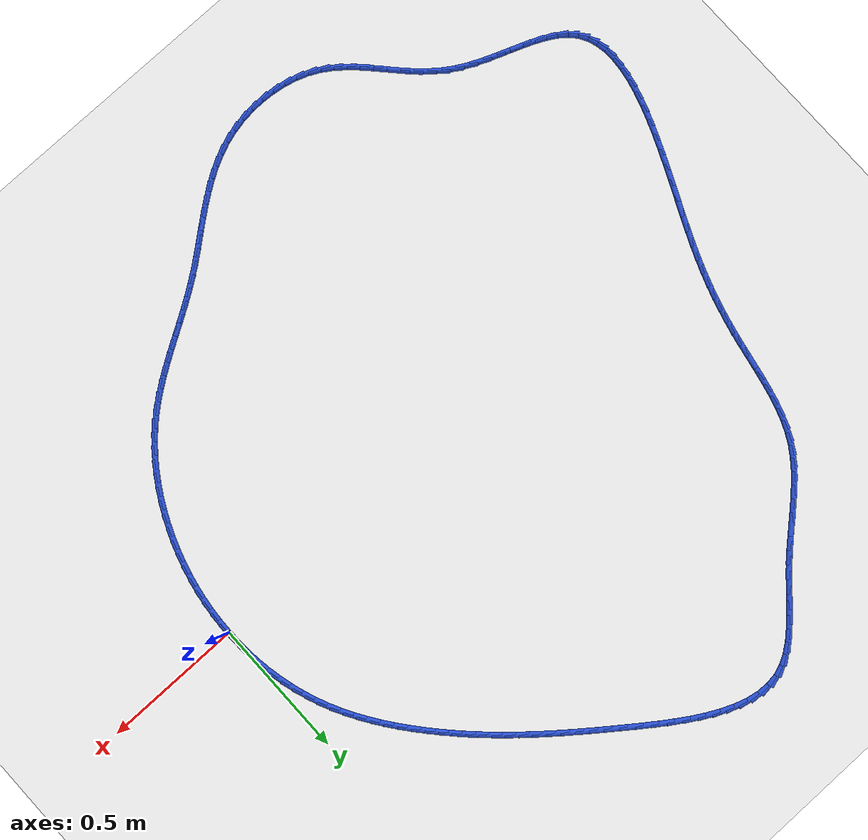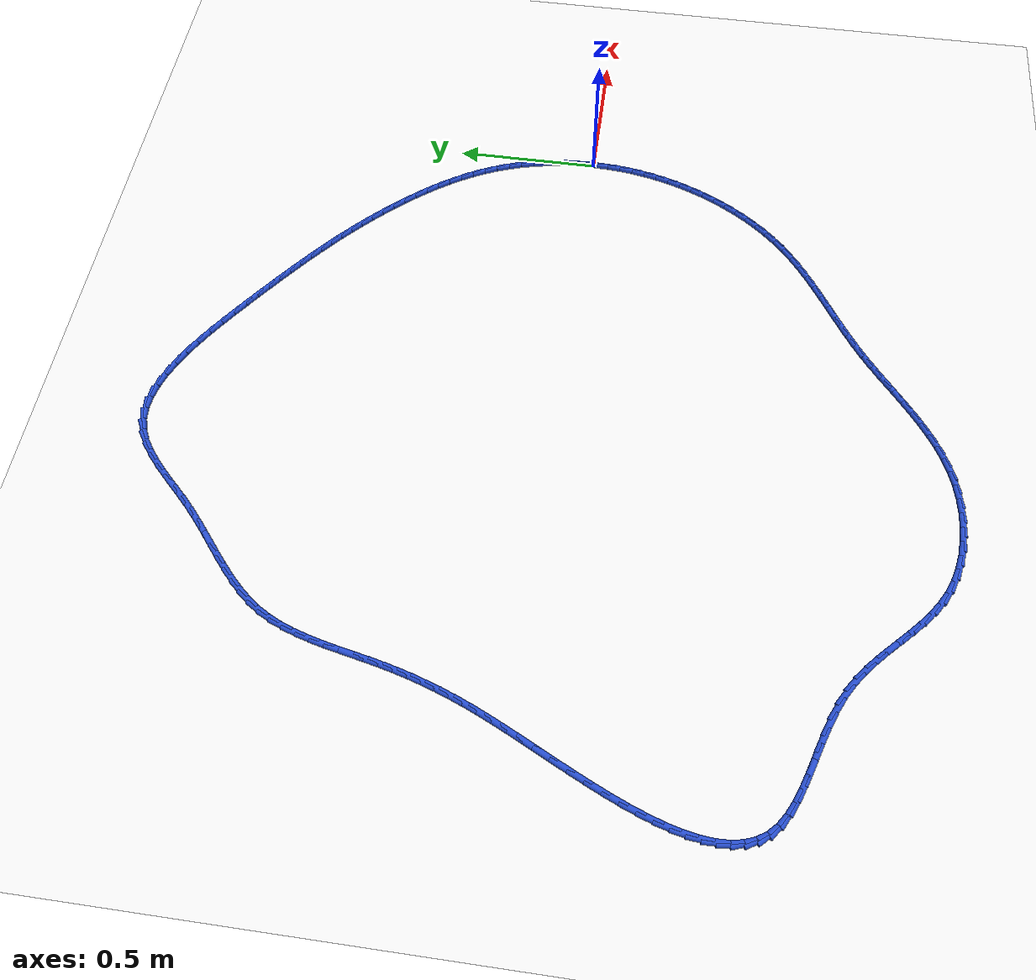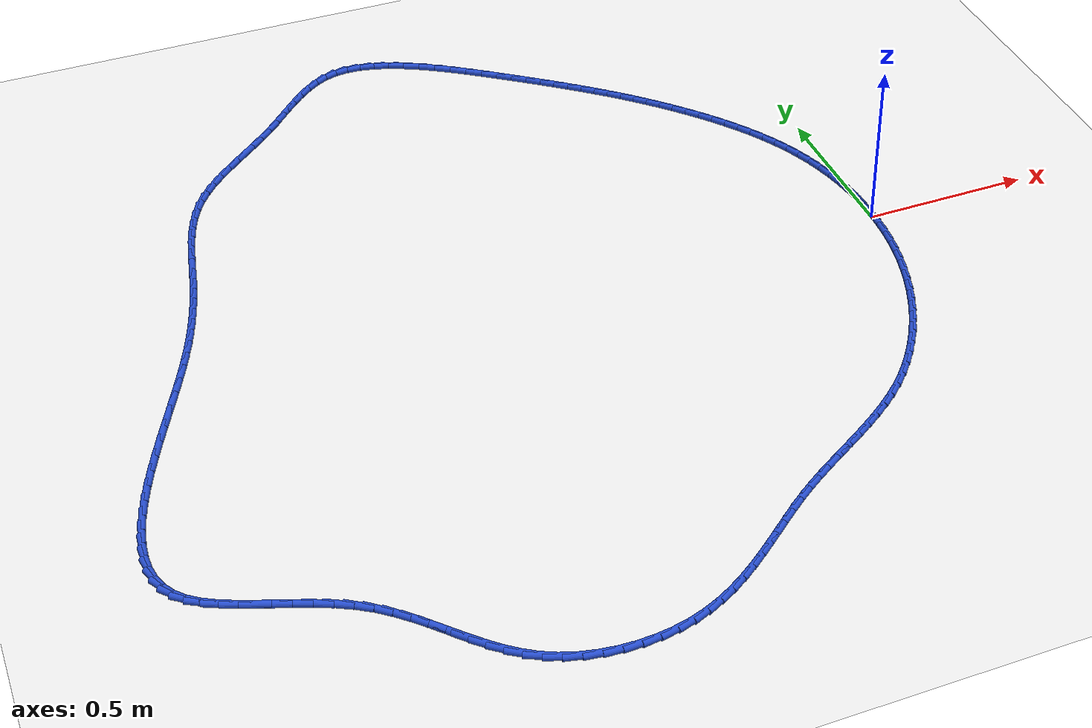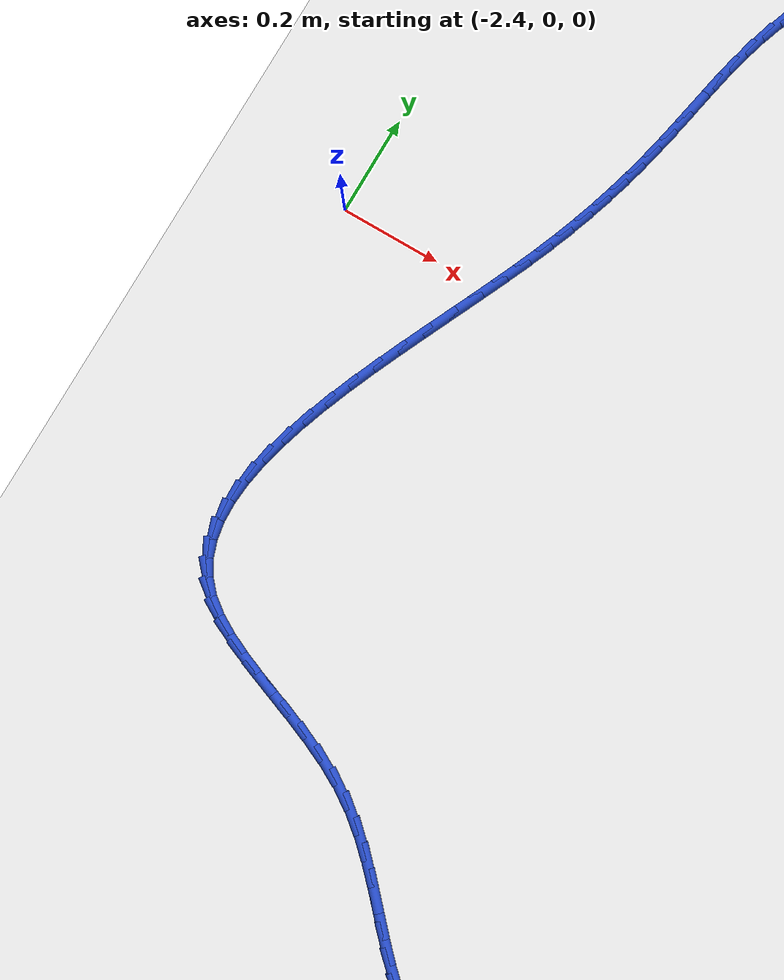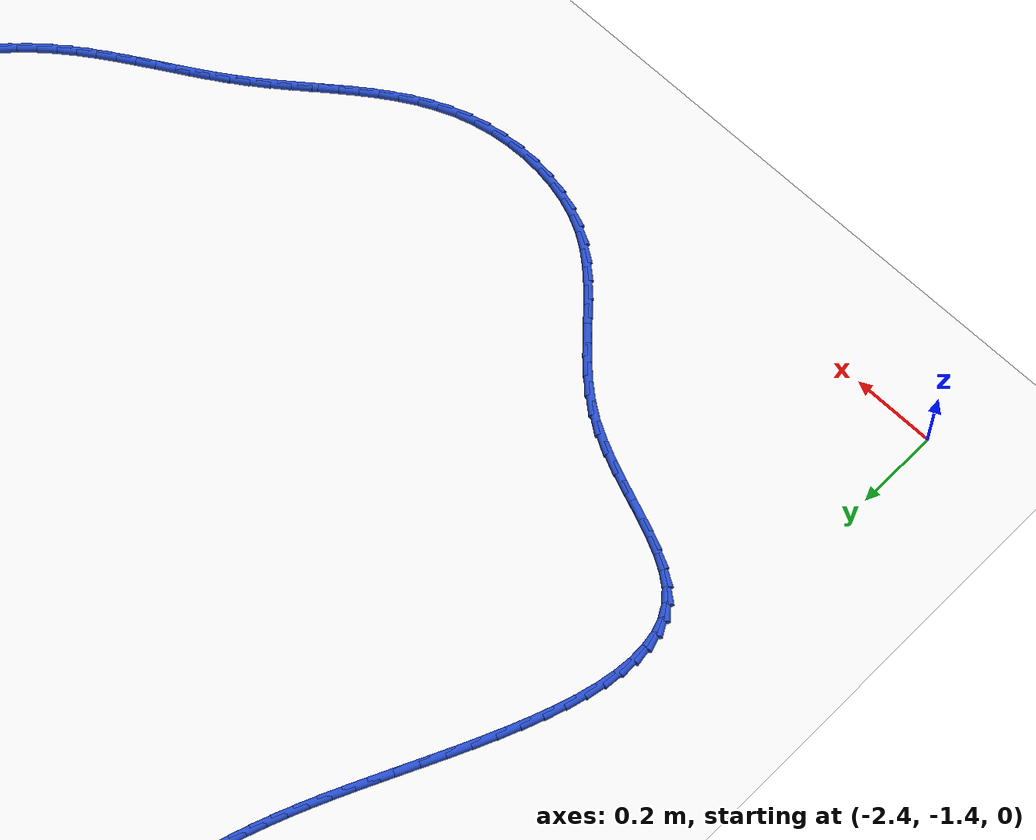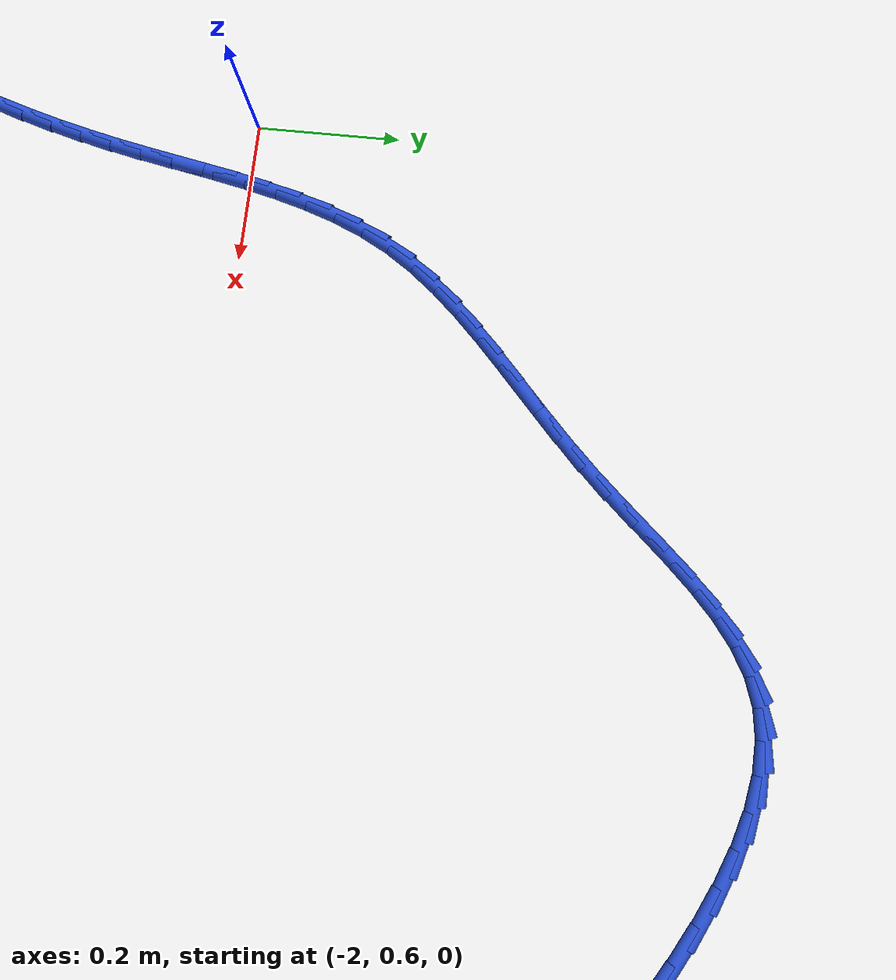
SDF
<sdf version="1.6">
 <world name="default">
  <light name="sun" type="directional">
   <pose>0 0 10 0 -0 0</pose>
   <diffuse>0.8 0.8 0.8 1</diffuse>
   <specular>0.2 0.2 0.2 1</specular>
   <attenuation>
    <range>1000</range>
    <constant>0.9</constant>
    <linear>0.01</linear>
    <quadratic>0.001</quadratic>
   </attenuation>
   <direction>-0.5 0.1 -0.9</direction>
  </light>
  <model name="ground_plane">
   <static>1</static>
   <link name="link">
    <collision name="collision">
     <geometry><plane><normal>0 0 1</normal><size>100 100</size></plane></geometry>
     <surface><friction><ode><mu>100</mu><mu2>50</mu2></ode></friction></surface>
    </collision>
    <visual name="visual">
     <cast_shadows>0</cast_shadows>
     <geometry><plane><normal>0 0 1</normal><size>100 100</size></plane></geometry>
     <material>
      <script><uri>file://media/materials/scripts/gazebo.material</uri><name>Gazebo/WhiteGlow</name></script>
     </material>
    </visual>
   </link>
  </model>
  <gravity>0 0 -9.8</gravity>
  <magnetic_field>6e-06 2.3e-05 -4.2e-05</magnetic_field>
  <atmosphere type="adiabatic"/>
  <physics name="default_physics" default="0" type="ode">
   <max_step_size>0.001</max_step_size>
   <real_time_factor>1</real_time_factor>
   <real_time_update_rate>1000</real_time_update_rate>
  </physics>
  <scene><ambient>0.4 0.4 0.4 1</ambient><background>0.7 0.7 0.7 1</background><shadows>1</shadows></scene>
  <spherical_coordinates>
   <surface_model>EARTH_WGS84</surface_model>
   <latitude_deg>0</latitude_deg>
   <longitude_deg>0</longitude_deg>
   <elevation>0</elevation>
   <heading_deg>0</heading_deg>
  </spherical_coordinates>
  <model name="line">
   <link name="link_0">
    <pose>-2.949029909160572e-17 1.3877787807814457e-17 0.01 0 1.57 -1.5533603134512748</pose>
    <collision name="collision">
     <geometry><cylinder><radius>0.01</radius><length>0.08</length></cylinder></geometry>
    </collision>
    <visual name="visual">
     <material>
      <script><name>Gazebo/Blue</name><uri>file://media/materials/scripts/gazebo.material</uri></script>
     </material>
     <geometry><cylinder><radius>0.01</radius><length>0.08</length></cylinder></geometry>
    </visual>
   </link>
   <link name="link_1">
    <pose>-0.0008119482922708272 0.0465625939390624 0.01 0 1.57 -1.5071413448697262</pose>
    <collision name="collision">
     <geometry><cylinder><radius>0.01</radius><length>0.08</length></cylinder></geometry>
    </collision>
    <visual name="visual">
     <material>
      <script><name>Gazebo/Blue</name><uri>file://media/materials/scripts/gazebo.material</uri></script>
     </material>
     <geometry><cylinder><radius>0.01</radius><length>0.08</length></cylinder></geometry>
    </visual>
   </link>
   <link name="link_2">
    <pose>-0.0037770765566050133 0.09308090618094901 0.01 0 1.57 -1.4602313086289629</pose>
    <collision name="collision">
     <geometry><cylinder><radius>0.01</radius><length>0.08</length></cylinder></geometry>
    </collision>
    <visual name="visual">
     <material>
      <script><name>Gazebo/Blue</name><uri>file://media/materials/scripts/gazebo.material</uri></script>
     </material>
     <geometry><cylinder><radius>0.01</radius><length>0.08</length></cylinder></geometry>
    </visual>
   </link>
   <link name="link_3">
    <pose>-0.008922433877695061 0.13942805660841073 0.01 0 1.57 -1.412463388067983</pose>
    <collision name="collision">
     <geometry><cylinder><radius>0.01</radius><length>0.08</length></cylinder></geometry>
    </collision>
    <visual name="visual">
     <material>
      <script><name>Gazebo/Blue</name><uri>file://media/materials/scripts/gazebo.material</uri></script>
     </material>
     <geometry><cylinder><radius>0.01</radius><length>0.08</length></cylinder></geometry>
    </visual>
   </link>
   <link name="link_4">
    <pose>-0.01627506934023347 0.18547716510419843 0.01 0 1.57 -1.3636806260696006</pose>
    <collision name="collision">
     <geometry><cylinder><radius>0.01</radius><length>0.08</length></cylinder></geometry>
    </collision>
    <visual name="visual">
     <material>
      <script><name>Gazebo/Blue</name><uri>file://media/materials/scripts/gazebo.material</uri></script>
     </material>
     <geometry><cylinder><radius>0.01</radius><length>0.08</length></cylinder></geometry>
    </visual>
   </link>
   <link name="link_5">
    <pose>-0.025862032028912706 0.23110135155106307 0.01 0 1.57 -1.313738531316304</pose>
    <collision name="collision">
     <geometry><cylinder><radius>0.01</radius><length>0.08</length></cylinder></geometry>
    </collision>
    <visual name="visual">
     <material>
      <script><name>Gazebo/Blue</name><uri>file://media/materials/scripts/gazebo.material</uri></script>
     </material>
     <geometry><cylinder><radius>0.01</radius><length>0.08</length></cylinder></geometry>
    </visual>
   </link>
   <link name="link_6">
    <pose>-0.037710371028425296 0.2761737358317557 0.01 0 1.57 -1.2625084227828178</pose>
    <collision name="collision">
     <geometry><cylinder><radius>0.01</radius><length>0.08</length></cylinder></geometry>
    </collision>
    <visual name="visual">
     <material>
      <script><name>Gazebo/Blue</name><uri>file://media/materials/scripts/gazebo.material</uri></script>
     </material>
     <geometry><cylinder><radius>0.01</radius><length>0.08</length></cylinder></geometry>
    </visual>
   </link>
   <link name="link_7">
    <pose>-0.05184713542346368 0.32056743782902697 0.01 0 1.57 -1.209881540126471</pose>
    <collision name="collision">
     <geometry><cylinder><radius>0.01</radius><length>0.08</length></cylinder></geometry>
    </collision>
    <visual name="visual">
     <material>
      <script><name>Gazebo/Blue</name><uri>file://media/materials/scripts/gazebo.material</uri></script>
     </material>
     <geometry><cylinder><radius>0.01</radius><length>0.08</length></cylinder></geometry>
    </visual>
   </link>
   <link name="link_8">
    <pose>-0.06829937429872035 0.36415557742562765 0.01 0 1.57 -1.1559580935545541</pose>
    <collision name="collision">
     <geometry><cylinder><radius>0.01</radius><length>0.08</length></cylinder></geometry>
    </collision>
    <visual name="visual">
     <material>
      <script><name>Gazebo/Blue</name><uri>file://media/materials/scripts/gazebo.material</uri></script>
     </material>
     <geometry><cylinder><radius>0.01</radius><length>0.08</length></cylinder></geometry>
    </visual>
   </link>
   <link name="link_9">
    <pose>-0.08708630432718735 0.4068147943207785 0.01 0 1.57 -1.1038081608523462</pose>
    <collision name="collision">
     <geometry><cylinder><radius>0.01</radius><length>0.08</length></cylinder></geometry>
    </collision>
    <visual name="visual">
     <material>
      <script><name>Gazebo/Blue</name><uri>file://media/materials/scripts/gazebo.material</uri></script>
     </material>
     <geometry><cylinder><radius>0.01</radius><length>0.08</length></cylinder></geometry>
    </visual>
   </link>
   <link name="link_10">
    <pose>-0.10809397328737348 0.4484815731357928 0.01 0 1.57 -1.0559559869276327</pose>
    <collision name="collision">
     <geometry><cylinder><radius>0.01</radius><length>0.08</length></cylinder></geometry>
    </collision>
    <visual name="visual">
     <material>
      <script><name>Gazebo/Blue</name><uri>file://media/materials/scripts/gazebo.material</uri></script>
     </material>
     <geometry><cylinder><radius>0.01</radius><length>0.08</length></cylinder></geometry>
    </visual>
   </link>
   <link name="link_11">
    <pose>-0.13109707784622399 0.48914243869560947 0.01 0 1.57 -1.0123253286820015</pose>
    <collision name="collision">
     <geometry><cylinder><radius>0.01</radius><length>0.08</length></cylinder></geometry>
    </collision>
    <visual name="visual">
     <material>
      <script><name>Gazebo/Blue</name><uri>file://media/materials/scripts/gazebo.material</uri></script>
     </material>
     <geometry><cylinder><radius>0.01</radius><length>0.08</length></cylinder></geometry>
    </visual>
   </link>
   <link name="link_12">
    <pose>-0.1558668896560805 0.5287854549964048 0.01 0 1.57 -0.9727207072776008</pose>
    <collision name="collision">
     <geometry><cylinder><radius>0.01</radius><length>0.08</length></cylinder></geometry>
    </collision>
    <visual name="visual">
     <material>
      <script><name>Gazebo/Blue</name><uri>file://media/materials/scripts/gazebo.material</uri></script>
     </material>
     <geometry><cylinder><radius>0.01</radius><length>0.08</length></cylinder></geometry>
    </visual>
   </link>
   <link name="link_13">
    <pose>-0.18217468036928475 0.5673986860343553 0.01 0 1.57 -0.9369302958949999</pose>
    <collision name="collision">
     <geometry><cylinder><radius>0.01</radius><length>0.08</length></cylinder></geometry>
    </collision>
    <visual name="visual">
     <material>
      <script><name>Gazebo/Blue</name><uri>file://media/materials/scripts/gazebo.material</uri></script>
     </material>
     <geometry><cylinder><radius>0.01</radius><length>0.08</length></cylinder></geometry>
    </visual>
   </link>
   <link name="link_14">
    <pose>-0.20979172163817839 0.6049701958056376 0.01 0 1.57 -0.904743029404285</pose>
    <collision name="collision">
     <geometry><cylinder><radius>0.01</radius><length>0.08</length></cylinder></geometry>
    </collision>
    <visual name="visual">
     <material>
      <script><name>Gazebo/Blue</name><uri>file://media/materials/scripts/gazebo.material</uri></script>
     </material>
     <geometry><cylinder><radius>0.01</radius><length>0.08</length></cylinder></geometry>
    </visual>
   </link>
   <link name="link_15">
    <pose>-0.23848928511510312 0.6414880483064276 0.01 0 1.57 -0.8759613745225202</pose>
    <collision name="collision">
     <geometry><cylinder><radius>0.01</radius><length>0.08</length></cylinder></geometry>
    </collision>
    <visual name="visual">
     <material>
      <script><name>Gazebo/Blue</name><uri>file://media/materials/scripts/gazebo.material</uri></script>
     </material>
     <geometry><cylinder><radius>0.01</radius><length>0.08</length></cylinder></geometry>
    </visual>
   </link>
   <link name="link_16">
    <pose>-0.2680386424524006 0.6769403075329019 0.01 0 1.57 -0.8504108662799478</pose>
    <collision name="collision">
     <geometry><cylinder><radius>0.01</radius><length>0.08</length></cylinder></geometry>
    </collision>
    <visual name="visual">
     <material>
      <script><name>Gazebo/Blue</name><uri>file://media/materials/scripts/gazebo.material</uri></script>
     </material>
     <geometry><cylinder><radius>0.01</radius><length>0.08</length></cylinder></geometry>
    </visual>
   </link>
   <link name="link_17">
    <pose>-0.2982110653024126 0.711315037481237 0.01 0 1.57 -0.8276167000107304</pose>
    <collision name="collision">
     <geometry><cylinder><radius>0.01</radius><length>0.08</length></cylinder></geometry>
    </collision>
    <visual name="visual">
     <material>
      <script><name>Gazebo/Blue</name><uri>file://media/materials/scripts/gazebo.material</uri></script>
     </material>
     <geometry><cylinder><radius>0.01</radius><length>0.08</length></cylinder></geometry>
    </visual>
   </link>
   <link name="link_18">
    <pose>-0.32881404460533525 0.7446176202141173 0.01 0 1.57 -0.8058158172791773</pose>
    <collision name="collision">
     <geometry><cylinder><radius>0.01</radius><length>0.08</length></cylinder></geometry>
    </collision>
    <visual name="visual">
     <material>
      <script><name>Gazebo/Blue</name><uri>file://media/materials/scripts/gazebo.material</uri></script>
     </material>
     <geometry><cylinder><radius>0.01</radius><length>0.08</length></cylinder></geometry>
    </visual>
   </link>
   <link name="link_19">
    <pose>-0.35984841018423835 0.7769458817883085 0.01 0 1.57 -0.7846309588125758</pose>
    <collision name="collision">
     <geometry><cylinder><radius>0.01</radius><length>0.08</length></cylinder></geometry>
    </collision>
    <visual name="visual">
     <material>
      <script><name>Gazebo/Blue</name><uri>file://media/materials/scripts/gazebo.material</uri></script>
     </material>
     <geometry><cylinder><radius>0.01</radius><length>0.08</length></cylinder></geometry>
    </visual>
   </link>
   <link name="link_20">
    <pose>-0.3913792413217872 0.8084283688097725 0.01 0 1.57 -0.7642879068218885</pose>
    <collision name="collision">
     <geometry><cylinder><radius>0.01</radius><length>0.08</length></cylinder></geometry>
    </collision>
    <visual name="visual">
     <material>
      <script><name>Gazebo/Blue</name><uri>file://media/materials/scripts/gazebo.material</uri></script>
     </material>
     <geometry><cylinder><radius>0.01</radius><length>0.08</length></cylinder></geometry>
    </visual>
   </link>
   <link name="link_21">
    <pose>-0.42347166020042754 0.8391936483967812 0.01 0 1.57 -0.7449963036001728</pose>
    <collision name="collision">
     <geometry><cylinder><radius>0.01</radius><length>0.08</length></cylinder></geometry>
    </collision>
    <visual name="visual">
     <material>
      <script><name>Gazebo/Blue</name><uri>file://media/materials/scripts/gazebo.material</uri></script>
     </material>
     <geometry><cylinder><radius>0.01</radius><length>0.08</length></cylinder></geometry>
    </visual>
   </link>
   <link name="link_22">
    <pose>-0.45619078900260485 0.8693702876676056 0.01 0 1.57 -0.7269421141589318</pose>
    <collision name="collision">
     <geometry><cylinder><radius>0.01</radius><length>0.08</length></cylinder></geometry>
    </collision>
    <visual name="visual">
     <material>
      <script><name>Gazebo/Blue</name><uri>file://media/materials/scripts/gazebo.material</uri></script>
     </material>
     <geometry><cylinder><radius>0.01</radius><length>0.08</length></cylinder></geometry>
    </visual>
   </link>
   <link name="link_23">
    <pose>-0.4896017499107646 0.8990868537405173 0.01 0 1.57 -0.7102819922520927</pose>
    <collision name="collision">
     <geometry><cylinder><radius>0.01</radius><length>0.08</length></cylinder></geometry>
    </collision>
    <visual name="visual">
     <material>
      <script><name>Gazebo/Blue</name><uri>file://media/materials/scripts/gazebo.material</uri></script>
     </material>
     <geometry><cylinder><radius>0.01</radius><length>0.08</length></cylinder></geometry>
    </visual>
   </link>
   <link name="link_24">
    <pose>-0.5237696651073526 0.9284719137337877 0.01 0 1.57 -0.6951394778932042</pose>
    <collision name="collision">
     <geometry><cylinder><radius>0.01</radius><length>0.08</length></cylinder></geometry>
    </collision>
    <visual name="visual">
     <material>
      <script><name>Gazebo/Blue</name><uri>file://media/materials/scripts/gazebo.material</uri></script>
     </material>
     <geometry><cylinder><radius>0.01</radius><length>0.08</length></cylinder></geometry>
    </visual>
   </link>
   <link name="link_25">
    <pose>-0.558759656774814 0.9576540347656877 0.01 0 1.57 -0.6816031345633323</pose>
    <collision name="collision">
     <geometry><cylinder><radius>0.01</radius><length>0.08</length></cylinder></geometry>
    </collision>
    <visual name="visual">
     <material>
      <script><name>Gazebo/Blue</name><uri>file://media/materials/scripts/gazebo.material</uri></script>
     </material>
     <geometry><cylinder><radius>0.01</radius><length>0.08</length></cylinder></geometry>
    </visual>
   </link>
   <link name="link_26">
    <pose>-0.5946368470955948 0.9867617839544894 0.01 0 1.57 -0.6697265370924608</pose>
    <collision name="collision">
     <geometry><cylinder><radius>0.01</radius><length>0.08</length></cylinder></geometry>
    </collision>
    <visual name="visual">
     <material>
      <script><name>Gazebo/Blue</name><uri>file://media/materials/scripts/gazebo.material</uri></script>
     </material>
     <geometry><cylinder><radius>0.01</radius><length>0.08</length></cylinder></geometry>
    </visual>
   </link>
   <link name="link_27">
    <pose>-0.6314663582521403 1.015923728418464 0.01 0 1.57 -0.6595298664703306</pose>
    <collision name="collision">
     <geometry><cylinder><radius>0.01</radius><length>0.08</length></cylinder></geometry>
    </collision>
    <visual name="visual">
     <material>
      <script><name>Gazebo/Blue</name><uri>file://media/materials/scripts/gazebo.material</uri></script>
     </material>
     <geometry><cylinder><radius>0.01</radius><length>0.08</length></cylinder></geometry>
    </visual>
   </link>
   <link name="link_28">
    <pose>-0.6693133124268964 1.0452684352758828 0.01 0 1.57 -0.6510027701788129</pose>
    <collision name="collision">
     <geometry><cylinder><radius>0.01</radius><length>0.08</length></cylinder></geometry>
    </collision>
    <visual name="visual">
     <material>
      <script><name>Gazebo/Blue</name><uri>file://media/materials/scripts/gazebo.material</uri></script>
     </material>
     <geometry><cylinder><radius>0.01</radius><length>0.08</length></cylinder></geometry>
    </visual>
   </link>
   <link name="link_29">
    <pose>-0.7082428318023082 1.0749244716450164 0.01 0 1.57 -0.6441081069986145</pose>
    <collision name="collision">
     <geometry><cylinder><radius>0.01</radius><length>0.08</length></cylinder></geometry>
    </collision>
    <visual name="visual">
     <material>
      <script><name>Gazebo/Blue</name><uri>file://media/materials/scripts/gazebo.material</uri></script>
     </material>
     <geometry><cylinder><radius>0.01</radius><length>0.08</length></cylinder></geometry>
    </visual>
   </link>
   <link name="link_30">
    <pose>-0.7483200385608214 1.1050204046441374 0.01 0 1.57 -0.6387521715640397</pose>
    <collision name="collision">
     <geometry><cylinder><radius>0.01</radius><length>0.08</length></cylinder></geometry>
    </collision>
    <visual name="visual">
     <material>
      <script><name>Gazebo/Blue</name><uri>file://media/materials/scripts/gazebo.material</uri></script>
     </material>
     <geometry><cylinder><radius>0.01</radius><length>0.08</length></cylinder></geometry>
    </visual>
   </link>
   <link name="link_31">
    <pose>-0.7896089052631333 1.1356817674740634 0.01 0 1.57 -0.6316781958866612</pose>
    <collision name="collision">
     <geometry><cylinder><radius>0.01</radius><length>0.08</length></cylinder></geometry>
    </collision>
    <visual name="visual">
     <material>
      <script><name>Gazebo/Blue</name><uri>file://media/materials/scripts/gazebo.material</uri></script>
     </material>
     <geometry><cylinder><radius>0.01</radius><length>0.08</length></cylinder></geometry>
    </visual>
   </link>
   <link name="link_32">
    <pose>-0.8320641528028798 1.166745771946449 0.01 0 1.57 -0.6171475268105038</pose>
    <collision name="collision">
     <geometry><cylinder><radius>0.01</radius><length>0.08</length></cylinder></geometry>
    </collision>
    <visual name="visual">
     <material>
      <script><name>Gazebo/Blue</name><uri>file://media/materials/scripts/gazebo.material</uri></script>
     </material>
     <geometry><cylinder><radius>0.01</radius><length>0.08</length></cylinder></geometry>
    </visual>
   </link>
   <link name="link_33">
    <pose>-0.8754427349582791 1.1975277111601084 0.01 0 1.57 -0.5942879000192868</pose>
    <collision name="collision">
     <geometry><cylinder><radius>0.01</radius><length>0.08</length></cylinder></geometry>
    </collision>
    <visual name="visual">
     <material>
      <script><name>Gazebo/Blue</name><uri>file://media/materials/scripts/gazebo.material</uri></script>
     </material>
     <geometry><cylinder><radius>0.01</radius><length>0.08</length></cylinder></geometry>
    </visual>
   </link>
   <link name="link_34">
    <pose>-0.9194807738372888 1.2272879022462637 0.01 0 1.57 -0.5622766533113347</pose>
    <collision name="collision">
     <geometry><cylinder><radius>0.01</radius><length>0.08</length></cylinder></geometry>
    </collision>
    <visual name="visual">
     <material>
      <script><name>Gazebo/Blue</name><uri>file://media/materials/scripts/gazebo.material</uri></script>
     </material>
     <geometry><cylinder><radius>0.01</radius><length>0.08</length></cylinder></geometry>
    </visual>
   </link>
   <link name="link_35">
    <pose>-0.9639143915478678 1.2552866623361374 0.01 0 1.57 -0.5196830151398898</pose>
    <collision name="collision">
     <geometry><cylinder><radius>0.01</radius><length>0.08</length></cylinder></geometry>
    </collision>
    <visual name="visual">
     <material>
      <script><name>Gazebo/Blue</name><uri>file://media/materials/scripts/gazebo.material</uri></script>
     </material>
     <geometry><cylinder><radius>0.01</radius><length>0.08</length></cylinder></geometry>
    </visual>
   </link>
   <link name="link_36">
    <pose>-1.0084797101979752 1.2807843085609527 0.01 0 1.57 -0.4643725459978044</pose>
    <collision name="collision">
     <geometry><cylinder><radius>0.01</radius><length>0.08</length></cylinder></geometry>
    </collision>
    <visual name="visual">
     <material>
      <script><name>Gazebo/Blue</name><uri>file://media/materials/scripts/gazebo.material</uri></script>
     </material>
     <geometry><cylinder><radius>0.01</radius><length>0.08</length></cylinder></geometry>
    </visual>
   </link>
   <link name="link_37">
    <pose>-1.0529128518955693 1.3030411580519314 0.01 0 1.57 -0.39338912335672166</pose>
    <collision name="collision">
     <geometry><cylinder><radius>0.01</radius><length>0.08</length></cylinder></geometry>
    </collision>
    <visual name="visual">
     <material>
      <script><name>Gazebo/Blue</name><uri>file://media/materials/scripts/gazebo.material</uri></script>
     </material>
     <geometry><cylinder><radius>0.01</radius><length>0.08</length></cylinder></geometry>
    </visual>
   </link>
   <link name="link_38">
    <pose>-1.0969499387486088 1.3213175279402967 0.01 0 1.57 -0.30290265232568686</pose>
    <collision name="collision">
     <geometry><cylinder><radius>0.01</radius><length>0.08</length></cylinder></geometry>
    </collision>
    <visual name="visual">
     <material>
      <script><name>Gazebo/Blue</name><uri>file://media/materials/scripts/gazebo.material</uri></script>
     </material>
     <geometry><cylinder><radius>0.01</radius><length>0.08</length></cylinder></geometry>
    </visual>
   </link>
   <link name="link_39">
    <pose>-1.140327092865052 1.3348737353572702 0.01 0 1.57 -0.18844904981153687</pose>
    <collision name="collision">
     <geometry><cylinder><radius>0.01</radius><length>0.08</length></cylinder></geometry>
    </collision>
    <visual name="visual">
     <material>
      <script><name>Gazebo/Blue</name><uri>file://media/materials/scripts/gazebo.material</uri></script>
     </material>
     <geometry><cylinder><radius>0.01</radius><length>0.08</length></cylinder></geometry>
    </visual>
   </link>
   <link name="link_40">
    <pose>-1.1827804363528576 1.3429700974340752 0.01 0 1.57 -0.04593407311028316</pose>
    <collision name="collision">
     <geometry><cylinder><radius>0.01</radius><length>0.08</length></cylinder></geometry>
    </collision>
    <visual name="visual">
     <material>
      <script><name>Gazebo/Blue</name><uri>file://media/materials/scripts/gazebo.material</uri></script>
     </material>
     <geometry><cylinder><radius>0.01</radius><length>0.08</length></cylinder></geometry>
    </visual>
   </link>
   <link name="link_41">
    <pose>-1.2240460913199849 1.3448669313019341 0.01 0 1.57 0.12597737258143998</pose>
    <collision name="collision">
     <geometry><cylinder><radius>0.01</radius><length>0.08</length></cylinder></geometry>
    </collision>
    <visual name="visual">
     <material>
      <script><name>Gazebo/Blue</name><uri>file://media/materials/scripts/gazebo.material</uri></script>
     </material>
     <geometry><cylinder><radius>0.01</radius><length>0.08</length></cylinder></geometry>
    </visual>
   </link>
   <link name="link_42">
    <pose>-1.2638601798743911 1.3398245540920688 0.01 0 1.57 0.3214975895071282</pose>
    <collision name="collision">
     <geometry><cylinder><radius>0.01</radius><length>0.08</length></cylinder></geometry>
    </collision>
    <visual name="visual">
     <material>
      <script><name>Gazebo/Blue</name><uri>file://media/materials/scripts/gazebo.material</uri></script>
     </material>
     <geometry><cylinder><radius>0.01</radius><length>0.08</length></cylinder></geometry>
    </visual>
   </link>
   <link name="link_43">
    <pose>-1.3019678682103324 1.3271327014185228 0.01 0 1.57 0.5047521227173826</pose>
    <collision name="collision">
     <geometry><cylinder><radius>0.01</radius><length>0.08</length></cylinder></geometry>
    </collision>
    <visual name="visual">
     <material>
      <script><name>Gazebo/Blue</name><uri>file://media/materials/scripts/gazebo.material</uri></script>
     </material>
     <geometry><cylinder><radius>0.01</radius><length>0.08</length></cylinder></geometry>
    </visual>
   </link>
   <link name="link_44">
    <pose>-1.3383984215444635 1.3070052223917503 0.01 0 1.57 0.6421266942492326</pose>
    <collision name="collision">
     <geometry><cylinder><radius>0.01</radius><length>0.08</length></cylinder></geometry>
    </collision>
    <visual name="visual">
     <material>
      <script><name>Gazebo/Blue</name><uri>file://media/materials/scripts/gazebo.material</uri></script>
     </material>
     <geometry><cylinder><radius>0.01</radius><length>0.08</length></cylinder></geometry>
    </visual>
   </link>
   <link name="link_45">
    <pose>-1.3735152673537965 1.2807429246487931 0.01 0 1.57 0.7371121310087629</pose>
    <collision name="collision">
     <geometry><cylinder><radius>0.01</radius><length>0.08</length></cylinder></geometry>
    </collision>
    <visual name="visual">
     <material>
      <script><name>Gazebo/Blue</name><uri>file://media/materials/scripts/gazebo.material</uri></script>
     </material>
     <geometry><cylinder><radius>0.01</radius><length>0.08</length></cylinder></geometry>
    </visual>
   </link>
   <link name="link_46">
    <pose>-1.4077009726042722 1.249708872500018 0.01 0 1.57 0.7972309260210882</pose>
    <collision name="collision">
     <geometry><cylinder><radius>0.01</radius><length>0.08</length></cylinder></geometry>
    </collision>
    <visual name="visual">
     <material>
      <script><name>Gazebo/Blue</name><uri>file://media/materials/scripts/gazebo.material</uri></script>
     </material>
     <geometry><cylinder><radius>0.01</radius><length>0.08</length></cylinder></geometry>
    </visual>
   </link>
   <link name="link_47">
    <pose>-1.4413381042618272 1.2152661302557919 0.01 0 1.57 0.8284998812565498</pose>
    <collision name="collision">
     <geometry><cylinder><radius>0.01</radius><length>0.08</length></cylinder></geometry>
    </collision>
    <visual name="visual">
     <material>
      <script><name>Gazebo/Blue</name><uri>file://media/materials/scripts/gazebo.material</uri></script>
     </material>
     <geometry><cylinder><radius>0.01</radius><length>0.08</length></cylinder></geometry>
    </visual>
   </link>
   <link name="link_48">
    <pose>-1.4748092292924015 1.178777762226481 0.01 0 1.57 0.8345162907589683</pose>
    <collision name="collision">
     <geometry><cylinder><radius>0.01</radius><length>0.08</length></cylinder></geometry>
    </collision>
    <visual name="visual">
     <material>
      <script><name>Gazebo/Blue</name><uri>file://media/materials/scripts/gazebo.material</uri></script>
     </material>
     <geometry><cylinder><radius>0.01</radius><length>0.08</length></cylinder></geometry>
    </visual>
   </link>
   <link name="link_49">
    <pose>-1.5084969146619327 1.1416068327224527 0.01 0 1.57 0.8165226095980469</pose>
    <collision name="collision">
     <geometry><cylinder><radius>0.01</radius><length>0.08</length></cylinder></geometry>
    </collision>
    <visual name="visual">
     <material>
      <script><name>Gazebo/Blue</name><uri>file://media/materials/scripts/gazebo.material</uri></script>
     </material>
     <geometry><cylinder><radius>0.01</radius><length>0.08</length></cylinder></geometry>
    </visual>
   </link>
   <link name="link_50">
    <pose>-1.54278372733636 1.105116406054074 0.01 0 1.57 0.7798641708995144</pose>
    <collision name="collision">
     <geometry><cylinder><radius>0.01</radius><length>0.08</length></cylinder></geometry>
    </collision>
    <visual name="visual">
     <material>
      <script><name>Gazebo/Blue</name><uri>file://media/materials/scripts/gazebo.material</uri></script>
     </material>
     <geometry><cylinder><radius>0.01</radius><length>0.08</length></cylinder></geometry>
    </visual>
   </link>
   <link name="link_51">
    <pose>-1.5779122068913187 1.0703745921263061 0.01 0 1.57 0.7499004616827907</pose>
    <collision name="collision">
     <geometry><cylinder><radius>0.01</radius><length>0.08</length></cylinder></geometry>
    </collision>
    <visual name="visual">
     <material>
      <script><name>Gazebo/Blue</name><uri>file://media/materials/scripts/gazebo.material</uri></script>
     </material>
     <geometry><cylinder><radius>0.01</radius><length>0.08</length></cylinder></geometry>
    </visual>
   </link>
   <link name="link_52">
    <pose>-1.6135311153927105 1.0371987648849026 0.01 0 1.57 0.7341058412489484</pose>
    <collision name="collision">
     <geometry><cylinder><radius>0.01</radius><length>0.08</length></cylinder></geometry>
    </collision>
    <visual name="visual">
     <material>
      <script><name>Gazebo/Blue</name><uri>file://media/materials/scripts/gazebo.material</uri></script>
     </material>
     <geometry><cylinder><radius>0.01</radius><length>0.08</length></cylinder></geometry>
    </visual>
   </link>
   <link name="link_53">
    <pose>-1.6491318536956892 1.0050748318228773 0.01 0 1.57 0.7331231672038031</pose>
    <collision name="collision">
     <geometry><cylinder><radius>0.01</radius><length>0.08</length></cylinder></geometry>
    </collision>
    <visual name="visual">
     <material>
      <script><name>Gazebo/Blue</name><uri>file://media/materials/scripts/gazebo.material</uri></script>
     </material>
     <geometry><cylinder><radius>0.01</radius><length>0.08</length></cylinder></geometry>
    </visual>
   </link>
   <link name="link_54">
    <pose>-1.6842058215620117 0.97348869813011 0.01 0 1.57 0.7476702004918352</pose>
    <collision name="collision">
     <geometry><cylinder><radius>0.01</radius><length>0.08</length></cylinder></geometry>
    </collision>
    <visual name="visual">
     <material>
      <script><name>Gazebo/Blue</name><uri>file://media/materials/scripts/gazebo.material</uri></script>
     </material>
     <geometry><cylinder><radius>0.01</radius><length>0.08</length></cylinder></geometry>
    </visual>
   </link>
   <link name="link_55">
    <pose>-1.718244418753437 0.9419262689964797 0.01 0 1.57 0.7785535858960803</pose>
    <collision name="collision">
     <geometry><cylinder><radius>0.01</radius><length>0.08</length></cylinder></geometry>
    </collision>
    <visual name="visual">
     <material>
      <script><name>Gazebo/Blue</name><uri>file://media/materials/scripts/gazebo.material</uri></script>
     </material>
     <geometry><cylinder><radius>0.01</radius><length>0.08</length></cylinder></geometry>
    </visual>
   </link>
   <link name="link_56">
    <pose>-1.7507390450317206 0.9098734496118646 0.01 0 1.57 0.8265603442760346</pose>
    <collision name="collision">
     <geometry><cylinder><radius>0.01</radius><length>0.08</length></cylinder></geometry>
    </collision>
    <visual name="visual">
     <material>
      <script><name>Gazebo/Blue</name><uri>file://media/materials/scripts/gazebo.material</uri></script>
     </material>
     <geometry><cylinder><radius>0.01</radius><length>0.08</length></cylinder></geometry>
    </visual>
   </link>
   <link name="link_57">
    <pose>-1.7811811001586215 0.876816145166145 0.01 0 1.57 0.8921845530803242</pose>
    <collision name="collision">
     <geometry><cylinder><radius>0.01</radius><length>0.08</length></cylinder></geometry>
    </collision>
    <visual name="visual">
     <material>
      <script><name>Gazebo/Blue</name><uri>file://media/materials/scripts/gazebo.material</uri></script>
     </material>
     <geometry><cylinder><radius>0.01</radius><length>0.08</length></cylinder></geometry>
    </visual>
   </link>
   <link name="link_58">
    <pose>-1.8090619838958961 0.8422402608491988 0.01 0 1.57 0.9751661863777186</pose>
    <collision name="collision">
     <geometry><cylinder><radius>0.01</radius><length>0.08</length></cylinder></geometry>
    </collision>
    <visual name="visual">
     <material>
      <script><name>Gazebo/Blue</name><uri>file://media/materials/scripts/gazebo.material</uri></script>
     </material>
     <geometry><cylinder><radius>0.01</radius><length>0.08</length></cylinder></geometry>
    </visual>
   </link>
   <link name="link_59">
    <pose>-1.833873096005302 0.805631701850906 0.01 0 1.57 1.072434941786886</pose>
    <collision name="collision">
     <geometry><cylinder><radius>0.01</radius><length>0.08</length></cylinder></geometry>
    </collision>
    <visual name="visual">
     <material>
      <script><name>Gazebo/Blue</name><uri>file://media/materials/scripts/gazebo.material</uri></script>
     </material>
     <geometry><cylinder><radius>0.01</radius><length>0.08</length></cylinder></geometry>
    </visual>
   </link>
   <link name="link_60">
    <pose>-1.8551552864347258 0.7665227341611508 0.01 0 1.57 1.1638056067535414</pose>
    <collision name="collision">
     <geometry><cylinder><radius>0.01</radius><length>0.08</length></cylinder></geometry>
    </collision>
    <visual name="visual">
     <material>
      <script><name>Gazebo/Blue</name><uri>file://media/materials/scripts/gazebo.material</uri></script>
     </material>
     <geometry><cylinder><radius>0.01</radius><length>0.08</length></cylinder></geometry>
    </visual>
   </link>
   <link name="link_61">
    <pose>-1.873050177657493 0.7250088632049151 0.01 0 1.57 1.2373509282849753</pose>
    <collision name="collision">
     <geometry><cylinder><radius>0.01</radius><length>0.08</length></cylinder></geometry>
    </collision>
    <visual name="visual">
     <material>
      <script><name>Gazebo/Blue</name><uri>file://media/materials/scripts/gazebo.material</uri></script>
     </material>
     <geometry><cylinder><radius>0.01</radius><length>0.08</length></cylinder></geometry>
    </visual>
   </link>
   <link name="link_62">
    <pose>-1.8880996580891216 0.6815608538500233 0.01 0 1.57 1.2940756208096322</pose>
    <collision name="collision">
     <geometry><cylinder><radius>0.01</radius><length>0.08</length></cylinder></geometry>
    </collision>
    <visual name="visual">
     <material>
      <script><name>Gazebo/Blue</name><uri>file://media/materials/scripts/gazebo.material</uri></script>
     </material>
     <geometry><cylinder><radius>0.01</radius><length>0.08</length></cylinder></geometry>
    </visual>
   </link>
   <link name="link_63">
    <pose>-1.9008528803271834 0.6366562813186688 0.01 0 1.57 1.335373713327469</pose>
    <collision name="collision">
     <geometry><cylinder><radius>0.01</radius><length>0.08</length></cylinder></geometry>
    </collision>
    <visual name="visual">
     <material>
      <script><name>Gazebo/Blue</name><uri>file://media/materials/scripts/gazebo.material</uri></script>
     </material>
     <geometry><cylinder><radius>0.01</radius><length>0.08</length></cylinder></geometry>
    </visual>
   </link>
   <link name="link_64">
    <pose>-1.9118589969692452 0.5907727208330461 0.01 0 1.57 1.3624145225281816</pose>
    <collision name="collision">
     <geometry><cylinder><radius>0.01</radius><length>0.08</length></cylinder></geometry>
    </collision>
    <visual name="visual">
     <material>
      <script><name>Gazebo/Blue</name><uri>file://media/materials/scripts/gazebo.material</uri></script>
     </material>
     <geometry><cylinder><radius>0.01</radius><length>0.08</length></cylinder></geometry>
    </visual>
   </link>
   <link name="link_65">
    <pose>-1.921667160612877 0.5443877476153486 0.01 0 1.57 1.375938016244257</pose>
    <collision name="collision">
     <geometry><cylinder><radius>0.01</radius><length>0.08</length></cylinder></geometry>
    </collision>
    <visual name="visual">
     <material>
      <script><name>Gazebo/Blue</name><uri>file://media/materials/scripts/gazebo.material</uri></script>
     </material>
     <geometry><cylinder><radius>0.01</radius><length>0.08</length></cylinder></geometry>
    </visual>
   </link>
   <link name="link_66">
    <pose>-1.9308265238556486 0.4979789368877697 0.01 0 1.57 1.3761495011889593</pose>
    <collision name="collision">
     <geometry><cylinder><radius>0.01</radius><length>0.08</length></cylinder></geometry>
    </collision>
    <visual name="visual">
     <material>
      <script><name>Gazebo/Blue</name><uri>file://media/materials/scripts/gazebo.material</uri></script>
     </material>
     <geometry><cylinder><radius>0.01</radius><length>0.08</length></cylinder></geometry>
    </visual>
   </link>
   <link name="link_67">
    <pose>-1.939886239295129 0.4520238638725042 0.01 0 1.57 1.3629282185330576</pose>
    <collision name="collision">
     <geometry><cylinder><radius>0.01</radius><length>0.08</length></cylinder></geometry>
    </collision>
    <visual name="visual">
     <material>
      <script><name>Gazebo/Blue</name><uri>file://media/materials/scripts/gazebo.material</uri></script>
     </material>
     <geometry><cylinder><radius>0.01</radius><length>0.08</length></cylinder></geometry>
    </visual>
   </link>
   <link name="link_68">
    <pose>-1.9493865817249383 0.4069803369674896 0.01 0 1.57 1.3414266242417359</pose>
    <collision name="collision">
     <geometry><cylinder><radius>0.01</radius><length>0.08</length></cylinder></geometry>
    </collision>
    <visual name="visual">
     <material>
      <script><name>Gazebo/Blue</name><uri>file://media/materials/scripts/gazebo.material</uri></script>
     </material>
     <geometry><cylinder><radius>0.01</radius><length>0.08</length></cylinder></geometry>
    </visual>
   </link>
   <link name="link_69">
    <pose>-1.9596807948858939 0.36288973163607324 0.01 0 1.57 1.317391326848597</pose>
    <collision name="collision">
     <geometry><cylinder><radius>0.01</radius><length>0.08</length></cylinder></geometry>
    </collision>
    <visual name="visual">
     <material>
      <script><name>Gazebo/Blue</name><uri>file://media/materials/scripts/gazebo.material</uri></script>
     </material>
     <geometry><cylinder><radius>0.01</radius><length>0.08</length></cylinder></geometry>
    </visual>
   </link>
   <link name="link_70">
    <pose>-1.970944154696322 0.31939717009129426 0.01 0 1.57 1.2916580364786892</pose>
    <collision name="collision">
     <geometry><cylinder><radius>0.01</radius><length>0.08</length></cylinder></geometry>
    </collision>
    <visual name="visual">
     <material>
      <script><name>Gazebo/Blue</name><uri>file://media/materials/scripts/gazebo.material</uri></script>
     </material>
     <geometry><cylinder><radius>0.01</radius><length>0.08</length></cylinder></geometry>
    </visual>
   </link>
   <link name="link_71">
    <pose>-1.9833448733187722 0.27613204678064845 0.01 0 1.57 1.2649507978252457</pose>
    <collision name="collision">
     <geometry><cylinder><radius>0.01</radius><length>0.08</length></cylinder></geometry>
    </collision>
    <visual name="visual">
     <material>
      <script><name>Gazebo/Blue</name><uri>file://media/materials/scripts/gazebo.material</uri></script>
     </material>
     <geometry><cylinder><radius>0.01</radius><length>0.08</length></cylinder></geometry>
    </visual>
   </link>
   <link name="link_72">
    <pose>-1.9970511629157939 0.2327237561516331 0.01 0 1.57 1.2380343368907398</pose>
    <collision name="collision">
     <geometry><cylinder><radius>0.01</radius><length>0.08</length></cylinder></geometry>
    </collision>
    <visual name="visual">
     <material>
      <script><name>Gazebo/Blue</name><uri>file://media/materials/scripts/gazebo.material</uri></script>
     </material>
     <geometry><cylinder><radius>0.01</radius><length>0.08</length></cylinder></geometry>
    </visual>
   </link>
   <link name="link_73">
    <pose>-2.0122312356499372 0.18880169265174374 0.01 0 1.57 1.211641181903166</pose>
    <collision name="collision">
     <geometry><cylinder><radius>0.01</radius><length>0.08</length></cylinder></geometry>
    </collision>
    <visual name="visual">
     <material>
      <script><name>Gazebo/Blue</name><uri>file://media/materials/scripts/gazebo.material</uri></script>
     </material>
     <geometry><cylinder><radius>0.01</radius><length>0.08</length></cylinder></geometry>
    </visual>
   </link>
   <link name="link_74">
    <pose>-2.029053303683752 0.14399525072847766 0.01 0 1.57 1.1864086704836174</pose>
    <collision name="collision">
     <geometry><cylinder><radius>0.01</radius><length>0.08</length></cylinder></geometry>
    </collision>
    <visual name="visual">
     <material>
      <script><name>Gazebo/Blue</name><uri>file://media/materials/scripts/gazebo.material</uri></script>
     </material>
     <geometry><cylinder><radius>0.01</radius><length>0.08</length></cylinder></geometry>
    </visual>
   </link>
   <link name="link_75">
    <pose>-2.0476855791559134 0.09793382485404102 0.01 0 1.57 1.1638982123588455</pose>
    <collision name="collision">
     <geometry><cylinder><radius>0.01</radius><length>0.08</length></cylinder></geometry>
    </collision>
    <visual name="visual">
     <material>
      <script><name>Gazebo/Blue</name><uri>file://media/materials/scripts/gazebo.material</uri></script>
     </material>
     <geometry><cylinder><radius>0.01</radius><length>0.08</length></cylinder></geometry>
    </visual>
   </link>
   <link name="link_76">
    <pose>-2.0681878599206396 0.05035902261180677 0.01 0 1.57 1.1479655688666335</pose>
    <collision name="collision">
     <geometry><cylinder><radius>0.01</radius><length>0.08</length></cylinder></geometry>
    </collision>
    <visual name="visual">
     <material>
      <script><name>Gazebo/Blue</name><uri>file://media/materials/scripts/gazebo.material</uri></script>
     </material>
     <geometry><cylinder><radius>0.01</radius><length>0.08</length></cylinder></geometry>
    </visual>
   </link>
   <link name="link_77">
    <pose>-2.0901941186797806 0.0014531976122891372 0.01 0 1.57 1.1385942545344012</pose>
    <collision name="collision">
     <geometry><cylinder><radius>0.01</radius><length>0.08</length></cylinder></geometry>
    </collision>
    <visual name="visual">
     <material>
      <script><name>Gazebo/Blue</name><uri>file://media/materials/scripts/gazebo.material</uri></script>
     </material>
     <geometry><cylinder><radius>0.01</radius><length>0.08</length></cylinder></geometry>
    </visual>
   </link>
   <link name="link_78">
    <pose>-2.1132337946085613 -0.04849310016206671 0.01 0 1.57 1.1350718296241256</pose>
    <collision name="collision">
     <geometry><cylinder><radius>0.01</radius><length>0.08</length></cylinder></geometry>
    </collision>
    <visual name="visual">
     <material>
      <script><name>Gazebo/Blue</name><uri>file://media/materials/scripts/gazebo.material</uri></script>
     </material>
     <geometry><cylinder><radius>0.01</radius><length>0.08</length></cylinder></geometry>
    </visual>
   </link>
   <link name="link_79">
    <pose>-2.136836326882205 -0.09918932072881387 0.01 0 1.57 1.137026792418814</pose>
    <collision name="collision">
     <geometry><cylinder><radius>0.01</radius><length>0.08</length></cylinder></geometry>
    </collision>
    <visual name="visual">
     <material>
      <script><name>Gazebo/Blue</name><uri>file://media/materials/scripts/gazebo.material</uri></script>
     </material>
     <geometry><cylinder><radius>0.01</radius><length>0.08</length></cylinder></geometry>
    </visual>
   </link>
   <link name="link_80">
    <pose>-2.1605311546759363 -0.15034491410550677 0.01 0 1.57 1.1443742118577038</pose>
    <collision name="collision">
     <geometry><cylinder><radius>0.01</radius><length>0.08</length></cylinder></geometry>
    </collision>
    <visual name="visual">
     <material>
      <script><name>Gazebo/Blue</name><uri>file://media/materials/scripts/gazebo.material</uri></script>
     </material>
     <geometry><cylinder><radius>0.01</radius><length>0.08</length></cylinder></geometry>
    </visual>
   </link>
   <link name="link_81">
    <pose>-2.1838477171649795 -0.20166933030969936 0.01 0 1.57 1.157295317608023</pose>
    <collision name="collision">
     <geometry><cylinder><radius>0.01</radius><length>0.08</length></cylinder></geometry>
    </collision>
    <visual name="visual">
     <material>
      <script><name>Gazebo/Blue</name><uri>file://media/materials/scripts/gazebo.material</uri></script>
     </material>
     <geometry><cylinder><radius>0.01</radius><length>0.08</length></cylinder></geometry>
    </visual>
   </link>
   <link name="link_82">
    <pose>-2.206315453524558 -0.2528720193589465 0.01 0 1.57 1.1762455039049775</pose>
    <collision name="collision">
     <geometry><cylinder><radius>0.01</radius><length>0.08</length></cylinder></geometry>
    </collision>
    <visual name="visual">
     <material>
      <script><name>Gazebo/Blue</name><uri>file://media/materials/scripts/gazebo.material</uri></script>
     </material>
     <geometry><cylinder><radius>0.01</radius><length>0.08</length></cylinder></geometry>
    </visual>
   </link>
   <link name="link_83">
    <pose>-2.227463802929895 -0.3036624312708003 0.01 0 1.57 1.2019895927054551</pose>
    <collision name="collision">
     <geometry><cylinder><radius>0.01</radius><length>0.08</length></cylinder></geometry>
    </collision>
    <visual name="visual">
     <material>
      <script><name>Gazebo/Blue</name><uri>file://media/materials/scripts/gazebo.material</uri></script>
     </material>
     <geometry><cylinder><radius>0.01</radius><length>0.08</length></cylinder></geometry>
    </visual>
   </link>
   <link name="link_84">
    <pose>-2.2468222045562163 -0.35375001606281564 0.01 0 1.57 1.2356662053786385</pose>
    <collision name="collision">
     <geometry><cylinder><radius>0.01</radius><length>0.08</length></cylinder></geometry>
    </collision>
    <visual name="visual">
     <material>
      <script><name>Gazebo/Blue</name><uri>file://media/materials/scripts/gazebo.material</uri></script>
     </material>
     <geometry><cylinder><radius>0.01</radius><length>0.08</length></cylinder></geometry>
    </visual>
   </link>
   <link name="link_85">
    <pose>-2.263920097578745 -0.40284422375254664 0.01 0 1.57 1.2788840591480641</pose>
    <collision name="collision">
     <geometry><cylinder><radius>0.01</radius><length>0.08</length></cylinder></geometry>
    </collision>
    <visual name="visual">
     <material>
      <script><name>Gazebo/Blue</name><uri>file://media/materials/scripts/gazebo.material</uri></script>
     </material>
     <geometry><cylinder><radius>0.01</radius><length>0.08</length></cylinder></geometry>
    </visual>
   </link>
   <link name="link_86">
    <pose>-2.278286921172704 -0.45065450435754706 0.01 0 1.57 1.3338489170531873</pose>
    <collision name="collision">
     <geometry><cylinder><radius>0.01</radius><length>0.08</length></cylinder></geometry>
    </collision>
    <visual name="visual">
     <material>
      <script><name>Gazebo/Blue</name><uri>file://media/materials/scripts/gazebo.material</uri></script>
     </material>
     <geometry><cylinder><radius>0.01</radius><length>0.08</length></cylinder></geometry>
    </visual>
   </link>
   <link name="link_87">
    <pose>-2.2894521145133195 -0.4968903078953719 0.01 0 1.57 1.403502240920932</pose>
    <collision name="collision">
     <geometry><cylinder><radius>0.01</radius><length>0.08</length></cylinder></geometry>
    </collision>
    <visual name="visual">
     <material>
      <script><name>Gazebo/Blue</name><uri>file://media/materials/scripts/gazebo.material</uri></script>
     </material>
     <geometry><cylinder><radius>0.01</radius><length>0.08</length></cylinder></geometry>
    </visual>
   </link>
   <link name="link_88">
    <pose>-2.296945116775814 -0.5412610843835732 0.01 0 1.57 1.4916010762462961</pose>
    <collision name="collision">
     <geometry><cylinder><radius>0.01</radius><length>0.08</length></cylinder></geometry>
    </collision>
    <visual name="visual">
     <material>
      <script><name>Gazebo/Blue</name><uri>file://media/materials/scripts/gazebo.material</uri></script>
     </material>
     <geometry><cylinder><radius>0.01</radius><length>0.08</length></cylinder></geometry>
    </visual>
   </link>
   <link name="link_89">
    <pose>-2.3002953671354116 -0.5834762838397061 0.01 0 1.57 -1.5390470838027503</pose>
    <collision name="collision">
     <geometry><cylinder><radius>0.01</radius><length>0.08</length></cylinder></geometry>
    </collision>
    <visual name="visual">
     <material>
      <script><name>Gazebo/Blue</name><uri>file://media/materials/scripts/gazebo.material</uri></script>
     </material>
     <geometry><cylinder><radius>0.01</radius><length>0.08</length></cylinder></geometry>
    </visual>
   </link>
   <link name="link_90">
    <pose>-2.2990323047673367 -0.6232453562813242 0.01 0 1.57 -1.4010567388194102</pose>
    <collision name="collision">
     <geometry><cylinder><radius>0.01</radius><length>0.08</length></cylinder></geometry>
    </collision>
    <visual name="visual">
     <material>
      <script><name>Gazebo/Blue</name><uri>file://media/materials/scripts/gazebo.material</uri></script>
     </material>
     <geometry><cylinder><radius>0.01</radius><length>0.08</length></cylinder></geometry>
    </visual>
   </link>
   <link name="link_91">
    <pose>-2.292685368846813 -0.6602777517259817 0.01 0 1.57 -1.2341329996178074</pose>
    <collision name="collision">
     <geometry><cylinder><radius>0.01</radius><length>0.08</length></cylinder></geometry>
    </collision>
    <visual name="visual">
     <material>
      <script><name>Gazebo/Blue</name><uri>file://media/materials/scripts/gazebo.material</uri></script>
     </material>
     <geometry><cylinder><radius>0.01</radius><length>0.08</length></cylinder></geometry>
    </visual>
   </link>
   <link name="link_92">
    <pose>-2.2807839985490648 -0.6942829201912333 0.01 0 1.57 -1.0421048540330218</pose>
    <collision name="collision">
     <geometry><cylinder><radius>0.01</radius><length>0.08</length></cylinder></geometry>
    </collision>
    <visual name="visual">
     <material>
      <script><name>Gazebo/Blue</name><uri>file://media/materials/scripts/gazebo.material</uri></script>
     </material>
     <geometry><cylinder><radius>0.01</radius><length>0.08</length></cylinder></geometry>
    </visual>
   </link>
   <link name="link_93">
    <pose>-2.262857633049316 -0.7249703116946313 0.01 0 1.57 -0.8371760394978309</pose>
    <collision name="collision">
     <geometry><cylinder><radius>0.01</radius><length>0.08</length></cylinder></geometry>
    </collision>
    <visual name="visual">
     <material>
      <script><name>Gazebo/Blue</name><uri>file://media/materials/scripts/gazebo.material</uri></script>
     </material>
     <geometry><cylinder><radius>0.01</radius><length>0.08</length></cylinder></geometry>
    </visual>
   </link>
   <link name="link_94">
    <pose>-2.2384426538342095 -0.7520541771854679 0.01 0 1.57 -0.6528817366957269</pose>
    <collision name="collision">
     <geometry><cylinder><radius>0.01</radius><length>0.08</length></cylinder></geometry>
    </collision>
    <visual name="visual">
     <material>
      <script><name>Gazebo/Blue</name><uri>file://media/materials/scripts/gazebo.material</uri></script>
     </material>
     <geometry><cylinder><radius>0.01</radius><length>0.08</length></cylinder></geometry>
    </visual>
   </link>
   <link name="link_95">
    <pose>-2.2076205508198092 -0.7756257354845395 0.01 0 1.57 -0.5211400893542413</pose>
    <collision name="collision">
     <geometry><cylinder><radius>0.01</radius><length>0.08</length></cylinder></geometry>
    </collision>
    <visual name="visual">
     <material>
      <script><name>Gazebo/Blue</name><uri>file://media/materials/scripts/gazebo.material</uri></script>
     </material>
     <geometry><cylinder><radius>0.01</radius><length>0.08</length></cylinder></geometry>
    </visual>
   </link>
   <link name="link_96">
    <pose>-2.1714013515798745 -0.7964183324566281 0.01 0 1.57 -0.43464366774029406</pose>
    <collision name="collision">
     <geometry><cylinder><radius>0.01</radius><length>0.08</length></cylinder></geometry>
    </collision>
    <visual name="visual">
     <material>
      <script><name>Gazebo/Blue</name><uri>file://media/materials/scripts/gazebo.material</uri></script>
     </material>
     <geometry><cylinder><radius>0.01</radius><length>0.08</length></cylinder></geometry>
    </visual>
   </link>
   <link name="link_97">
    <pose>-2.1308855995491047 -0.8152279099008156 0.01 0 1.57 -0.383220970406036</pose>
    <collision name="collision">
     <geometry><cylinder><radius>0.01</radius><length>0.08</length></cylinder></geometry>
    </collision>
    <visual name="visual">
     <material>
      <script><name>Gazebo/Blue</name><uri>file://media/materials/scripts/gazebo.material</uri></script>
     </material>
     <geometry><cylinder><radius>0.01</radius><length>0.08</length></cylinder></geometry>
    </visual>
   </link>
   <link name="link_98">
    <pose>-2.0871738381621965 -0.8328504096161842 0.01 0 1.57 -0.359797158968006</pose>
    <collision name="collision">
     <geometry><cylinder><radius>0.01</radius><length>0.08</length></cylinder></geometry>
    </collision>
    <visual name="visual">
     <material>
      <script><name>Gazebo/Blue</name><uri>file://media/materials/scripts/gazebo.material</uri></script>
     </material>
     <geometry><cylinder><radius>0.01</radius><length>0.08</length></cylinder></geometry>
    </visual>
   </link>
   <link name="link_99">
    <pose>-2.0413666108538457 -0.8500817734018158 0.01 0 1.57 -0.36036876573139587</pose>
    <collision name="collision">
     <geometry><cylinder><radius>0.01</radius><length>0.08</length></cylinder></geometry>
    </collision>
    <visual name="visual">
     <material>
      <script><name>Gazebo/Blue</name><uri>file://media/materials/scripts/gazebo.material</uri></script>
     </material>
     <geometry><cylinder><radius>0.01</radius><length>0.08</length></cylinder></geometry>
    </visual>
   </link>
   <link name="link_100">
    <pose>-1.994564461058751 -0.8677179430567928 0.01 0 1.57 -0.3834254542363489</pose>
    <collision name="collision">
     <geometry><cylinder><radius>0.01</radius><length>0.08</length></cylinder></geometry>
    </collision>
    <visual name="visual">
     <material>
      <script><name>Gazebo/Blue</name><uri>file://media/materials/scripts/gazebo.material</uri></script>
     </material>
     <geometry><cylinder><radius>0.01</radius><length>0.08</length></cylinder></geometry>
    </visual>
   </link>
   <link name="link_101">
    <pose>-1.9478679322116075 -0.8865548603801975 0.01 0 1.57 -0.429468967834059</pose>
    <collision name="collision">
     <geometry><cylinder><radius>0.01</radius><length>0.08</length></cylinder></geometry>
    </collision>
    <visual name="visual">
     <material>
      <script><name>Gazebo/Blue</name><uri>file://media/materials/scripts/gazebo.material</uri></script>
     </material>
     <geometry><cylinder><radius>0.01</radius><length>0.08</length></cylinder></geometry>
    </visual>
   </link>
   <link name="link_102">
    <pose>-1.902377567747115 -0.9073884671711115 0.01 0 1.57 -0.5006221867058577</pose>
    <collision name="collision">
     <geometry><cylinder><radius>0.01</radius><length>0.08</length></cylinder></geometry>
    </collision>
    <visual name="visual">
     <material>
      <script><name>Gazebo/Blue</name><uri>file://media/materials/scripts/gazebo.material</uri></script>
     </material>
     <geometry><cylinder><radius>0.01</radius><length>0.08</length></cylinder></geometry>
    </visual>
   </link>
   <link name="link_103">
    <pose>-1.859193911099969 -0.9310147052286172 0.01 0 1.57 -0.5958788762497915</pose>
    <collision name="collision">
     <geometry><cylinder><radius>0.01</radius><length>0.08</length></cylinder></geometry>
    </collision>
    <visual name="visual">
     <material>
      <script><name>Gazebo/Blue</name><uri>file://media/materials/scripts/gazebo.material</uri></script>
     </material>
     <geometry><cylinder><radius>0.01</radius><length>0.08</length></cylinder></geometry>
    </visual>
   </link>
   <link name="link_104">
    <pose>-1.8192646306228215 -0.9580909018978079 0.01 0 1.57 -0.685535855952169</pose>
    <collision name="collision">
     <geometry><cylinder><radius>0.01</radius><length>0.08</length></cylinder></geometry>
    </collision>
    <visual name="visual">
     <material>
      <script><name>Gazebo/Blue</name><uri>file://media/materials/scripts/gazebo.material</uri></script>
     </material>
     <geometry><cylinder><radius>0.01</radius><length>0.08</length></cylinder></geometry>
    </visual>
   </link>
   <link name="link_105">
    <pose>-1.7823987631496432 -0.9882419678333296 0.01 0 1.57 -0.7536825500894747</pose>
    <collision name="collision">
     <geometry><cylinder><radius>0.01</radius><length>0.08</length></cylinder></geometry>
    </collision>
    <visual name="visual">
     <material>
      <script><name>Gazebo/Blue</name><uri>file://media/materials/scripts/gazebo.material</uri></script>
     </material>
     <geometry><cylinder><radius>0.01</radius><length>0.08</length></cylinder></geometry>
    </visual>
   </link>
   <link name="link_106">
    <pose>-1.7478915478844887 -1.0206269445829819 0.01 0 1.57 -0.7992021872696775</pose>
    <collision name="collision">
     <geometry><cylinder><radius>0.01</radius><length>0.08</length></cylinder></geometry>
    </collision>
    <visual name="visual">
     <material>
      <script><name>Gazebo/Blue</name><uri>file://media/materials/scripts/gazebo.material</uri></script>
     </material>
     <geometry><cylinder><radius>0.01</radius><length>0.08</length></cylinder></geometry>
    </visual>
   </link>
   <link name="link_107">
    <pose>-1.715035725386945 -1.0544026081308477 0.01 0 1.57 -0.8217894862395425</pose>
    <collision name="collision">
     <geometry><cylinder><radius>0.01</radius><length>0.08</length></cylinder></geometry>
    </collision>
    <visual name="visual">
     <material>
      <script><name>Gazebo/Blue</name><uri>file://media/materials/scripts/gazebo.material</uri></script>
     </material>
     <geometry><cylinder><radius>0.01</radius><length>0.08</length></cylinder></geometry>
    </visual>
   </link>
   <link name="link_108">
    <pose>-1.683124036216597 -1.088725734461012 0.01 0 1.57 -0.8211891398843412</pose>
    <collision name="collision">
     <geometry><cylinder><radius>0.01</radius><length>0.08</length></cylinder></geometry>
    </collision>
    <visual name="visual">
     <material>
      <script><name>Gazebo/Blue</name><uri>file://media/materials/scripts/gazebo.material</uri></script>
     </material>
     <geometry><cylinder><radius>0.01</radius><length>0.08</length></cylinder></geometry>
    </visual>
   </link>
   <link name="link_109">
    <pose>-1.6514492209330325 -1.1227530995575592 0.01 0 1.57 -0.79682528541398</pose>
    <collision name="collision">
     <geometry><cylinder><radius>0.01</radius><length>0.08</length></cylinder></geometry>
    </collision>
    <visual name="visual">
     <material>
      <script><name>Gazebo/Blue</name><uri>file://media/materials/scripts/gazebo.material</uri></script>
     </material>
     <geometry><cylinder><radius>0.01</radius><length>0.08</length></cylinder></geometry>
    </visual>
   </link>
   <link name="link_110">
    <pose>-1.6193040200958366 -1.1556414794045735 0.01 0 1.57 -0.747789993198343</pose>
    <collision name="collision">
     <geometry><cylinder><radius>0.01</radius><length>0.08</length></cylinder></geometry>
    </collision>
    <visual name="visual">
     <material>
      <script><name>Gazebo/Blue</name><uri>file://media/materials/scripts/gazebo.material</uri></script>
     </material>
     <geometry><cylinder><radius>0.01</radius><length>0.08</length></cylinder></geometry>
    </visual>
   </link>
   <link name="link_111">
    <pose>-1.5859811742645953 -1.1865476499861392 0.01 0 1.57 -0.6732590732783226</pose>
    <collision name="collision">
     <geometry><cylinder><radius>0.01</radius><length>0.08</length></cylinder></geometry>
    </collision>
    <visual name="visual">
     <material>
      <script><name>Gazebo/Blue</name><uri>file://media/materials/scripts/gazebo.material</uri></script>
     </material>
     <geometry><cylinder><radius>0.01</radius><length>0.08</length></cylinder></geometry>
    </visual>
   </link>
   <link name="link_112">
    <pose>-1.5507734239988957 -1.2146283872863401 0.01 0 1.57 -0.5734337206090842</pose>
    <collision name="collision">
     <geometry><cylinder><radius>0.01</radius><length>0.08</length></cylinder></geometry>
    </collision>
    <visual name="visual">
     <material>
      <script><name>Gazebo/Blue</name><uri>file://media/materials/scripts/gazebo.material</uri></script>
     </material>
     <geometry><cylinder><radius>0.01</radius><length>0.08</length></cylinder></geometry>
    </visual>
   </link>
   <link name="link_113">
    <pose>-1.5129735098583246 -1.2390404672892612 0.01 0 1.57 -0.4541753199523095</pose>
    <collision name="collision">
     <geometry><cylinder><radius>0.01</radius><length>0.08</length></cylinder></geometry>
    </collision>
    <visual name="visual">
     <material>
      <script><name>Gazebo/Blue</name><uri>file://media/materials/scripts/gazebo.material</uri></script>
     </material>
     <geometry><cylinder><radius>0.01</radius><length>0.08</length></cylinder></geometry>
    </visual>
   </link>
   <link name="link_114">
    <pose>-1.472017440064246 -1.2590358390488339 0.01 0 1.57 -0.33880938456993753</pose>
    <collision name="collision">
     <geometry><cylinder><radius>0.01</radius><length>0.08</length></cylinder></geometry>
    </collision>
    <visual name="visual">
     <material>
      <script><name>Gazebo/Blue</name><uri>file://media/materials/scripts/gazebo.material</uri></script>
     </material>
     <geometry><cylinder><radius>0.01</radius><length>0.08</length></cylinder></geometry>
    </visual>
   </link>
   <link name="link_115">
    <pose>-1.4282394128113227 -1.2744631214885411 0.01 0 1.57 -0.2338578049598133</pose>
    <collision name="collision">
     <geometry><cylinder><radius>0.01</radius><length>0.08</length></cylinder></geometry>
    </collision>
    <visual name="visual">
     <material>
      <script><name>Gazebo/Blue</name><uri>file://media/materials/scripts/gazebo.material</uri></script>
     </material>
     <geometry><cylinder><radius>0.01</radius><length>0.08</length></cylinder></geometry>
    </visual>
   </link>
   <link name="link_116">
    <pose>-1.382320937997426 -1.285401653574186 0.01 0 1.57 -0.13696067001255066</pose>
    <collision name="collision">
     <geometry><cylinder><radius>0.01</radius><length>0.08</length></cylinder></geometry>
    </collision>
    <visual name="visual">
     <material>
      <script><name>Gazebo/Blue</name><uri>file://media/materials/scripts/gazebo.material</uri></script>
     </material>
     <geometry><cylinder><radius>0.01</radius><length>0.08</length></cylinder></geometry>
    </visual>
   </link>
   <link name="link_117">
    <pose>-1.33494427512014 -1.2919312722325507 0.01 0 1.57 -0.04566757708014233</pose>
    <collision name="collision">
     <geometry><cylinder><radius>0.01</radius><length>0.08</length></cylinder></geometry>
    </collision>
    <visual name="visual">
     <material>
      <script><name>Gazebo/Blue</name><uri>file://media/materials/scripts/gazebo.material</uri></script>
     </material>
     <geometry><cylinder><radius>0.01</radius><length>0.08</length></cylinder></geometry>
    </visual>
   </link>
   <link name="link_118">
    <pose>-1.2867916836770468 -1.294131814390419 0.01 0 1.57 0.04243784627135929</pose>
    <collision name="collision">
     <geometry><cylinder><radius>0.01</radius><length>0.08</length></cylinder></geometry>
    </collision>
    <visual name="visual">
     <material>
      <script><name>Gazebo/Blue</name><uri>file://media/materials/scripts/gazebo.material</uri></script>
     </material>
     <geometry><cylinder><radius>0.01</radius><length>0.08</length></cylinder></geometry>
    </visual>
   </link>
   <link name="link_119">
    <pose>-1.2385454231657282 -1.2920831169745757 0.01 0 1.57 0.12974137097983587</pose>
    <collision name="collision">
     <geometry><cylinder><radius>0.01</radius><length>0.08</length></cylinder></geometry>
    </collision>
    <visual name="visual">
     <material>
      <script><name>Gazebo/Blue</name><uri>file://media/materials/scripts/gazebo.material</uri></script>
     </material>
     <geometry><cylinder><radius>0.01</radius><length>0.08</length></cylinder></geometry>
    </visual>
   </link>
   <link name="link_120">
    <pose>-1.190887753083766 -1.285865016911802 0.01 0 1.57 0.21865833574234425</pose>
    <collision name="collision">
     <geometry><cylinder><radius>0.01</radius><length>0.08</length></cylinder></geometry>
    </collision>
    <visual name="visual">
     <material>
      <script><name>Gazebo/Blue</name><uri>file://media/materials/scripts/gazebo.material</uri></script>
     </material>
     <geometry><cylinder><radius>0.01</radius><length>0.08</length></cylinder></geometry>
    </visual>
   </link>
   <link name="link_121">
    <pose>-1.1445009329287426 -1.2755573511288831 0.01 0 1.57 0.31097961404792573</pose>
    <collision name="collision">
     <geometry><cylinder><radius>0.01</radius><length>0.08</length></cylinder></geometry>
    </collision>
    <visual name="visual">
     <material>
      <script><name>Gazebo/Blue</name><uri>file://media/materials/scripts/gazebo.material</uri></script>
     </material>
     <geometry><cylinder><radius>0.01</radius><length>0.08</length></cylinder></geometry>
    </visual>
   </link>
   <link name="link_122">
    <pose>-1.1000191727415436 -1.261260558598877 0.01 0 1.57 0.3996078558520396</pose>
    <collision name="collision">
     <geometry><cylinder><radius>0.01</radius><length>0.08</length></cylinder></geometry>
    </collision>
    <visual name="visual">
     <material>
      <script><name>Gazebo/Blue</name><uri>file://media/materials/scripts/gazebo.material</uri></script>
     </material>
     <geometry><cylinder><radius>0.01</radius><length>0.08</length></cylinder></geometry>
    </visual>
   </link>
   <link name="link_123">
    <pose>-1.057522264728132 -1.2433127946536922 0.01 0 1.57 0.4775546692220771</pose>
    <collision name="collision">
     <geometry><cylinder><radius>0.01</radius><length>0.08</length></cylinder></geometry>
    </collision>
    <visual name="visual">
     <material>
      <script><name>Gazebo/Blue</name><uri>file://media/materials/scripts/gazebo.material</uri></script>
     </material>
     <geometry><cylinder><radius>0.01</radius><length>0.08</length></cylinder></geometry>
    </visual>
   </link>
   <link name="link_124">
    <pose>-1.0167342762764864 -1.2222047378724308 0.01 0 1.57 0.5433781524849339</pose>
    <collision name="collision">
     <geometry><cylinder><radius>0.01</radius><length>0.08</length></cylinder></geometry>
    </collision>
    <visual name="visual">
     <material>
      <script><name>Gazebo/Blue</name><uri>file://media/materials/scripts/gazebo.material</uri></script>
     </material>
     <geometry><cylinder><radius>0.01</radius><length>0.08</length></cylinder></geometry>
    </visual>
   </link>
   <link name="link_125">
    <pose>-0.977373433648831 -1.198429571319184 0.01 0 1.57 0.5965066593585788</pose>
    <collision name="collision">
     <geometry><cylinder><radius>0.01</radius><length>0.08</length></cylinder></geometry>
    </collision>
    <visual name="visual">
     <material>
      <script><name>Gazebo/Blue</name><uri>file://media/materials/scripts/gazebo.material</uri></script>
     </material>
     <geometry><cylinder><radius>0.01</radius><length>0.08</length></cylinder></geometry>
    </visual>
   </link>
   <link name="link_126">
    <pose>-0.9391579631073919 -1.1724804780580438 0.01 0 1.57 0.6368878225001757</pose>
    <collision name="collision">
     <geometry><cylinder><radius>0.01</radius><length>0.08</length></cylinder></geometry>
    </collision>
    <visual name="visual">
     <material>
      <script><name>Gazebo/Blue</name><uri>file://media/materials/scripts/gazebo.material</uri></script>
     </material>
     <geometry><cylinder><radius>0.01</radius><length>0.08</length></cylinder></geometry>
    </visual>
   </link>
   <link name="link_127">
    <pose>-0.9018060909143945 -1.1448506411531025 0.01 0 1.57 0.664734574453249</pose>
    <collision name="collision">
     <geometry><cylinder><radius>0.01</radius><length>0.08</length></cylinder></geometry>
    </collision>
    <visual name="visual">
     <material>
      <script><name>Gazebo/Blue</name><uri>file://media/materials/scripts/gazebo.material</uri></script>
     </material>
     <geometry><cylinder><radius>0.01</radius><length>0.08</length></cylinder></geometry>
    </visual>
   </link>
   <link name="link_128">
    <pose>-0.8650360433320641 -1.116033243668451 0.01 0 1.57 0.6803297803828365</pose>
    <collision name="collision">
     <geometry><cylinder><radius>0.01</radius><length>0.08</length></cylinder></geometry>
    </collision>
    <visual name="visual">
     <material>
      <script><name>Gazebo/Blue</name><uri>file://media/materials/scripts/gazebo.material</uri></script>
     </material>
     <geometry><cylinder><radius>0.01</radius><length>0.08</length></cylinder></geometry>
    </visual>
   </link>
   <link name="link_129">
    <pose>-0.8285660466226253 -1.086521468668181 0.01 0 1.57 0.683900011944958</pose>
    <collision name="collision">
     <geometry><cylinder><radius>0.01</radius><length>0.08</length></cylinder></geometry>
    </collision>
    <visual name="visual">
     <material>
      <script><name>Gazebo/Blue</name><uri>file://media/materials/scripts/gazebo.material</uri></script>
     </material>
     <geometry><cylinder><radius>0.01</radius><length>0.08</length></cylinder></geometry>
    </visual>
   </link>
   <link name="link_130">
    <pose>-0.7921143270483043 -1.0568084992163844 0.01 0 1.57 0.6755510047324416</pose>
    <collision name="collision">
     <geometry><cylinder><radius>0.01</radius><length>0.08</length></cylinder></geometry>
    </collision>
    <visual name="visual">
     <material>
      <script><name>Gazebo/Blue</name><uri>file://media/materials/scripts/gazebo.material</uri></script>
     </material>
     <geometry><cylinder><radius>0.01</radius><length>0.08</length></cylinder></geometry>
    </visual>
   </link>
   <link name="link_131">
    <pose>-0.7553991108713252 -1.0273875183771524 0.01 0 1.57 0.6552553427552141</pose>
    <collision name="collision">
     <geometry><cylinder><radius>0.01</radius><length>0.08</length></cylinder></geometry>
    </collision>
    <visual name="visual">
     <material>
      <script><name>Gazebo/Blue</name><uri>file://media/materials/scripts/gazebo.material</uri></script>
     </material>
     <geometry><cylinder><radius>0.01</radius><length>0.08</length></cylinder></geometry>
    </visual>
   </link>
   <link name="link_132">
    <pose>-0.7181386243539148 -0.9987517092145769 0.01 0 1.57 0.6235650302302163</pose>
    <collision name="collision">
     <geometry><cylinder><radius>0.01</radius><length>0.08</length></cylinder></geometry>
    </collision>
    <visual name="visual">
     <material>
      <script><name>Gazebo/Blue</name><uri>file://media/materials/scripts/gazebo.material</uri></script>
     </material>
     <geometry><cylinder><radius>0.01</radius><length>0.08</length></cylinder></geometry>
    </visual>
   </link>
   <link name="link_133">
    <pose>-0.6800682289707252 -0.9713674923154364 0.01 0 1.57 0.5915161205449849</pose>
    <collision name="collision">
     <geometry><cylinder><radius>0.01</radius><length>0.08</length></cylinder></geometry>
    </collision>
    <visual name="visual">
     <material>
      <script><name>Gazebo/Blue</name><uri>file://media/materials/scripts/gazebo.material</uri></script>
     </material>
     <geometry><cylinder><radius>0.01</radius><length>0.08</length></cylinder></geometry>
    </visual>
   </link>
   <link name="link_134">
    <pose>-0.6412051437085031 -0.9452610716479648 0.01 0 1.57 0.5682664327566278</pose>
    <collision name="collision">
     <geometry><cylinder><radius>0.01</radius><length>0.08</length></cylinder></geometry>
    </collision>
    <visual name="visual">
     <material>
      <script><name>Gazebo/Blue</name><uri>file://media/materials/scripts/gazebo.material</uri></script>
     </material>
     <geometry><cylinder><radius>0.01</radius><length>0.08</length></cylinder></geometry>
    </visual>
   </link>
   <link name="link_135">
    <pose>-0.6017973706998316 -0.9200982046011209 0.01 0 1.57 0.5541147682399344</pose>
    <collision name="collision">
     <geometry><cylinder><radius>0.01</radius><length>0.08</length></cylinder></geometry>
    </collision>
    <visual name="visual">
     <material>
      <script><name>Gazebo/Blue</name><uri>file://media/materials/scripts/gazebo.material</uri></script>
     </material>
     <geometry><cylinder><radius>0.01</radius><length>0.08</length></cylinder></geometry>
    </visual>
   </link>
   <link name="link_136">
    <pose>-0.5620997042591345 -0.895534040255783 0.01 0 1.57 0.5490839060345821</pose>
    <collision name="collision">
     <geometry><cylinder><radius>0.01</radius><length>0.08</length></cylinder></geometry>
    </collision>
    <visual name="visual">
     <material>
      <script><name>Gazebo/Blue</name><uri>file://media/materials/scripts/gazebo.material</uri></script>
     </material>
     <geometry><cylinder><radius>0.01</radius><length>0.08</length></cylinder></geometry>
    </visual>
   </link>
   <link name="link_137">
    <pose>-0.5223669387008378 -0.8712237276928312 0.01 0 1.57 0.5532243421522898</pose>
    <collision name="collision">
     <geometry><cylinder><radius>0.01</radius><length>0.08</length></cylinder></geometry>
    </collision>
    <visual name="visual">
     <material>
      <script><name>Gazebo/Blue</name><uri>file://media/materials/scripts/gazebo.material</uri></script>
     </material>
     <geometry><cylinder><radius>0.01</radius><length>0.08</length></cylinder></geometry>
    </visual>
   </link>
   <link name="link_138">
    <pose>-0.48285386833936567 -0.846822415993144 0.01 0 1.57 0.566627629237763</pose>
    <collision name="collision">
     <geometry><cylinder><radius>0.01</radius><length>0.08</length></cylinder></geometry>
    </collision>
    <visual name="visual">
     <material>
      <script><name>Gazebo/Blue</name><uri>file://media/materials/scripts/gazebo.material</uri></script>
     </material>
     <geometry><cylinder><radius>0.01</radius><length>0.08</length></cylinder></geometry>
    </visual>
   </link>
   <link name="link_139">
    <pose>-0.4438152874891427 -0.8219852542376003 0.01 0 1.57 0.5894168360414056</pose>
    <collision name="collision">
     <geometry><cylinder><radius>0.01</radius><length>0.08</length></cylinder></geometry>
    </collision>
    <visual name="visual">
     <material>
      <script><name>Gazebo/Blue</name><uri>file://media/materials/scripts/gazebo.material</uri></script>
     </material>
     <geometry><cylinder><radius>0.01</radius><length>0.08</length></cylinder></geometry>
    </visual>
   </link>
   <link name="link_140">
    <pose>-0.4055059904645933 -0.7963673915070794 0.01 0 1.57 0.6217123135581637</pose>
    <collision name="collision">
     <geometry><cylinder><radius>0.01</radius><length>0.08</length></cylinder></geometry>
    </collision>
    <visual name="visual">
     <material>
      <script><name>Gazebo/Blue</name><uri>file://media/materials/scripts/gazebo.material</uri></script>
     </material>
     <geometry><cylinder><radius>0.01</radius><length>0.08</length></cylinder></geometry>
    </visual>
   </link>
   <link name="link_141">
    <pose>-0.3681807715801416 -0.7696239768824594 0.01 0 1.57 0.6635704428972542</pose>
    <collision name="collision">
     <geometry><cylinder><radius>0.01</radius><length>0.08</length></cylinder></geometry>
    </collision>
    <visual name="visual">
     <material>
      <script><name>Gazebo/Blue</name><uri>file://media/materials/scripts/gazebo.material</uri></script>
     </material>
     <geometry><cylinder><radius>0.01</radius><length>0.08</length></cylinder></geometry>
    </visual>
   </link>
   <link name="link_142">
    <pose>-0.33209442515021365 -0.7414101594446206 0.01 0 1.57 0.7148948968306144</pose>
    <collision name="collision">
     <geometry><cylinder><radius>0.01</radius><length>0.08</length></cylinder></geometry>
    </collision>
    <visual name="visual">
     <material>
      <script><name>Gazebo/Blue</name><uri>file://media/materials/scripts/gazebo.material</uri></script>
     </material>
     <geometry><cylinder><radius>0.01</radius><length>0.08</length></cylinder></geometry>
    </visual>
   </link>
   <link name="link_143">
    <pose>-0.2975017454892333 -0.7113810882744415 0.01 0 1.57 0.7740704382260165</pose>
    <collision name="collision">
     <geometry><cylinder><radius>0.01</radius><length>0.08</length></cylinder></geometry>
    </collision>
    <visual name="visual">
     <material>
      <script><name>Gazebo/Blue</name><uri>file://media/materials/scripts/gazebo.material</uri></script>
     </material>
     <geometry><cylinder><radius>0.01</radius><length>0.08</length></cylinder></geometry>
    </visual>
   </link>
   <link name="link_144">
    <pose>-0.26463286229204736 -0.6792485547573003 0.01 0 1.57 0.8331280483922394</pose>
    <collision name="collision">
     <geometry><cylinder><radius>0.01</radius><length>0.08</length></cylinder></geometry>
    </collision>
    <visual name="visual">
     <material>
      <script><name>Gazebo/Blue</name><uri>file://media/materials/scripts/gazebo.material</uri></script>
     </material>
     <geometry><cylinder><radius>0.01</radius><length>0.08</length></cylinder></geometry>
    </visual>
   </link>
   <link name="link_145">
    <pose>-0.23356843575250283 -0.6450676070217913 0.01 0 1.57 0.8893460614570877</pose>
    <collision name="collision">
     <geometry><cylinder><radius>0.01</radius><length>0.08</length></cylinder></geometry>
    </collision>
    <visual name="visual">
     <material>
      <script><name>Gazebo/Blue</name><uri>file://media/materials/scripts/gazebo.material</uri></script>
     </material>
     <geometry><cylinder><radius>0.01</radius><length>0.08</length></cylinder></geometry>
    </visual>
   </link>
   <link name="link_146">
    <pose>-0.204333117013331 -0.6090219179951987 0.01 0 1.57 0.9429684310340805</pose>
    <collision name="collision">
     <geometry><cylinder><radius>0.01</radius><length>0.08</length></cylinder></geometry>
    </collision>
    <visual name="visual">
     <material>
      <script><name>Gazebo/Blue</name><uri>file://media/materials/scripts/gazebo.material</uri></script>
     </material>
     <geometry><cylinder><radius>0.01</radius><length>0.08</length></cylinder></geometry>
    </visual>
   </link>
   <link name="link_147">
    <pose>-0.1769514585580527 -0.5712953871757128 0.01 0 1.57 0.9942743667953864</pose>
    <collision name="collision">
     <geometry><cylinder><radius>0.01</radius><length>0.08</length></cylinder></geometry>
    </collision>
    <visual name="visual">
     <material>
      <script><name>Gazebo/Blue</name><uri>file://media/materials/scripts/gazebo.material</uri></script>
     </material>
     <geometry><cylinder><radius>0.01</radius><length>0.08</length></cylinder></geometry>
    </visual>
   </link>
   <link name="link_148">
    <pose>-0.1514480128701869 -0.5320719140615207 0.01 0 1.57 1.0435619795307214</pose>
    <collision name="collision">
     <geometry><cylinder><radius>0.01</radius><length>0.08</length></cylinder></geometry>
    </collision>
    <visual name="visual">
     <material>
      <script><name>Gazebo/Blue</name><uri>file://media/materials/scripts/gazebo.material</uri></script>
     </material>
     <geometry><cylinder><radius>0.01</radius><length>0.08</length></cylinder></geometry>
    </visual>
   </link>
   <link name="link_149">
    <pose>-0.12784733243325316 -0.4915353981508108 0.01 0 1.57 1.091140644822912</pose>
    <collision name="collision">
     <geometry><cylinder><radius>0.01</radius><length>0.08</length></cylinder></geometry>
    </collision>
    <visual name="visual">
     <material>
      <script><name>Gazebo/Blue</name><uri>file://media/materials/scripts/gazebo.material</uri></script>
     </material>
     <geometry><cylinder><radius>0.01</radius><length>0.08</length></cylinder></geometry>
    </visual>
   </link>
   <link name="link_150">
    <pose>-0.10617396973077127 -0.44986973894177157 0.01 0 1.57 1.1373265028836337</pose>
    <collision name="collision">
     <geometry><cylinder><radius>0.01</radius><length>0.08</length></cylinder></geometry>
    </collision>
    <visual name="visual">
     <material>
      <script><name>Gazebo/Blue</name><uri>file://media/materials/scripts/gazebo.material</uri></script>
     </material>
     <geometry><cylinder><radius>0.01</radius><length>0.08</length></cylinder></geometry>
    </visual>
   </link>
   <link name="link_151">
    <pose>-0.08645247724626039 -0.4072588359325904 0.01 0 1.57 1.1824508170493455</pose>
    <collision name="collision">
     <geometry><cylinder><radius>0.01</radius><length>0.08</length></cylinder></geometry>
    </collision>
    <visual name="visual">
     <material>
      <script><name>Gazebo/Blue</name><uri>file://media/materials/scripts/gazebo.material</uri></script>
     </material>
     <geometry><cylinder><radius>0.01</radius><length>0.08</length></cylinder></geometry>
    </visual>
   </link>
   <link name="link_152">
    <pose>-0.06870729428409529 -0.3638850380186749 0.01 0 1.57 1.227124993653231</pose>
    <collision name="collision">
     <geometry><cylinder><radius>0.01</radius><length>0.08</length></cylinder></geometry>
    </collision>
    <visual name="visual">
     <material>
      <script><name>Gazebo/Blue</name><uri>file://media/materials/scripts/gazebo.material</uri></script>
     </material>
     <geometry><cylinder><radius>0.01</radius><length>0.08</length></cylinder></geometry>
    </visual>
   </link>
   <link name="link_153">
    <pose>-0.05295918056618654 -0.31988028223931053 0.01 0 1.57 1.2718328546621105</pose>
    <collision name="collision">
     <geometry><cylinder><radius>0.01</radius><length>0.08</length></cylinder></geometry>
    </collision>
    <visual name="visual">
     <material>
      <script><name>Gazebo/Blue</name><uri>file://media/materials/scripts/gazebo.material</uri></script>
     </material>
     <geometry><cylinder><radius>0.01</radius><length>0.08</length></cylinder></geometry>
    </visual>
   </link>
   <link name="link_154">
    <pose>-0.039224495266288184 -0.27531621623878766 0.01 0 1.57 1.3166198506818227</pose>
    <collision name="collision">
     <geometry><cylinder><radius>0.01</radius><length>0.08</length></cylinder></geometry>
    </collision>
    <visual name="visual">
     <material>
      <script><name>Gazebo/Blue</name><uri>file://media/materials/scripts/gazebo.material</uri></script>
     </material>
     <geometry><cylinder><radius>0.01</radius><length>0.08</length></cylinder></geometry>
    </visual>
   </link>
   <link name="link_155">
    <pose>-0.027519338737166 -0.23026094170297537 0.01 0 1.57 1.3615083152504224</pose>
    <collision name="collision">
     <geometry><cylinder><radius>0.01</radius><length>0.08</length></cylinder></geometry>
    </collision>
    <visual name="visual">
     <material>
      <script><name>Gazebo/Blue</name><uri>file://media/materials/scripts/gazebo.material</uri></script>
     </material>
     <geometry><cylinder><radius>0.01</radius><length>0.08</length></cylinder></geometry>
    </visual>
   </link>
   <link name="link_156">
    <pose>-0.017859811331585592 -0.18478256031774218 0.01 0 1.57 1.4065202628038163</pose>
    <collision name="collision">
     <geometry><cylinder><radius>0.01</radius><length>0.08</length></cylinder></geometry>
    </collision>
    <visual name="visual">
     <material>
      <script><name>Gazebo/Blue</name><uri>file://media/materials/scripts/gazebo.material</uri></script>
     </material>
     <geometry><cylinder><radius>0.01</radius><length>0.08</length></cylinder></geometry>
    </visual>
   </link>
   <link name="link_157">
    <pose>-0.010262013402313136 -0.1389491737689593 0.01 0 1.57 1.4516766327529835</pose>
    <collision name="collision">
     <geometry><cylinder><radius>0.01</radius><length>0.08</length></cylinder></geometry>
    </collision>
    <visual name="visual">
     <material>
      <script><name>Gazebo/Blue</name><uri>file://media/materials/scripts/gazebo.material</uri></script>
     </material>
     <geometry><cylinder><radius>0.01</radius><length>0.08</length></cylinder></geometry>
    </visual>
   </link>
   <link name="link_158">
    <pose>-0.004742045302114192 -0.09282888374249502 0.01 0 1.57 1.4969965250573003</pose>
    <collision name="collision">
     <geometry><cylinder><radius>0.01</radius><length>0.08</length></cylinder></geometry>
    </collision>
    <visual name="visual">
     <material>
      <script><name>Gazebo/Blue</name><uri>file://media/materials/scripts/gazebo.material</uri></script>
     </material>
     <geometry><cylinder><radius>0.01</radius><length>0.08</length></cylinder></geometry>
    </visual>
   </link>
   <link name="link_159">
    <pose>-0.001316007383754557 -0.046489791924218773 0.01 0 1.57 1.542496435839709</pose>
    <collision name="collision">
     <geometry><cylinder><radius>0.01</radius><length>0.08</length></cylinder></geometry>
    </collision>
    <visual name="visual">
     <material>
      <script><name>Gazebo/Blue</name><uri>file://media/materials/scripts/gazebo.material</uri></script>
     </material>
     <geometry><cylinder><radius>0.01</radius><length>0.08</length></cylinder></geometry>
    </visual>
   </link>
   <link name="link_160">
    <pose>-2.42861286636753e-17 1.1102230246251565e-16 0.01 0 1.57 -1.553403150227695</pose>
    <collision name="collision">
     <geometry><cylinder><radius>0.01</radius><length>0.08</length></cylinder></geometry>
    </collision>
    <visual name="visual">
     <material>
      <script><name>Gazebo/Blue</name><uri>file://media/materials/scripts/gazebo.material</uri></script>
     </material>
     <geometry><cylinder><radius>0.01</radius><length>0.08</length></cylinder></geometry>
    </visual>
   </link>
   <link name="link_161">
    <pose>-0.0008101235036164084 0.04657239034429314 0.01 0 1.57 -1.5534031502276953</pose>
    <collision name="collision">
     <geometry><cylinder><radius>0.01</radius><length>0.08</length></cylinder></geometry>
    </collision>
    <visual name="visual">
     <material>
      <script><name>Gazebo/Blue</name><uri>file://media/materials/scripts/gazebo.material</uri></script>
     </material>
     <geometry><cylinder><radius>0.01</radius><length>0.08</length></cylinder></geometry>
    </visual>
   </link>
  </model>
 </world>
</sdf>
